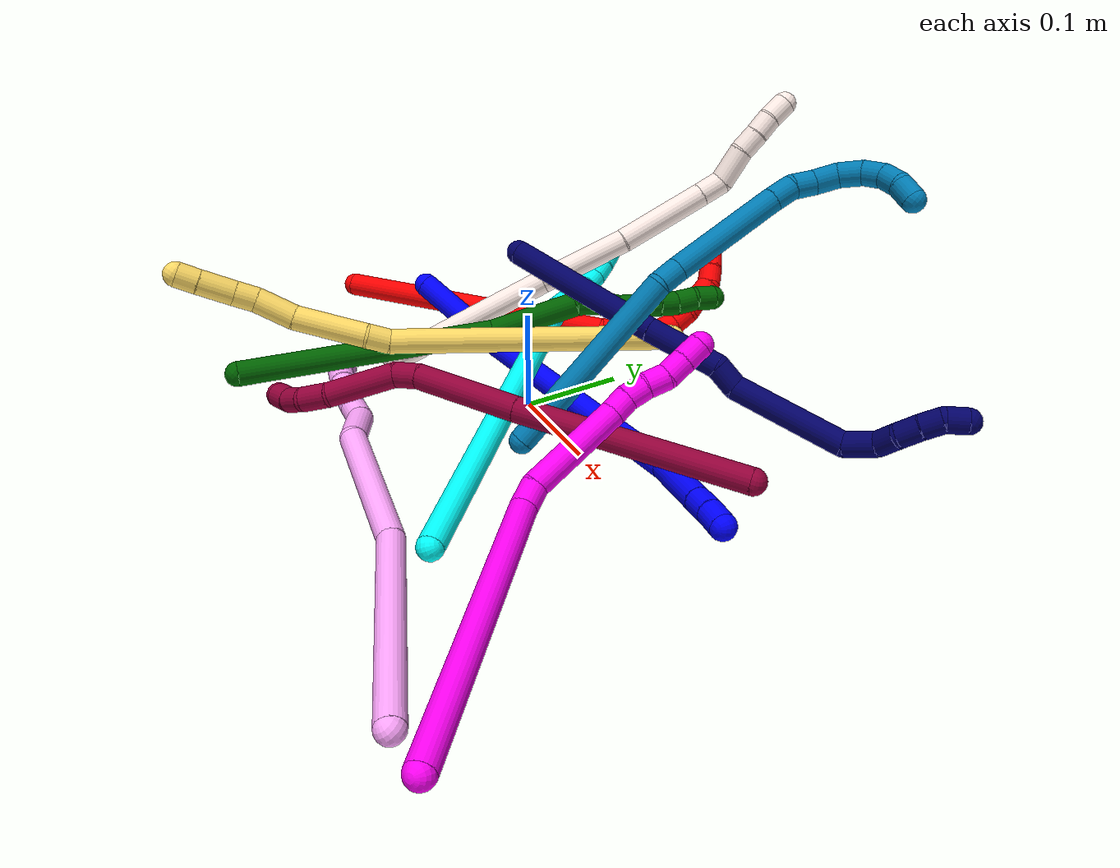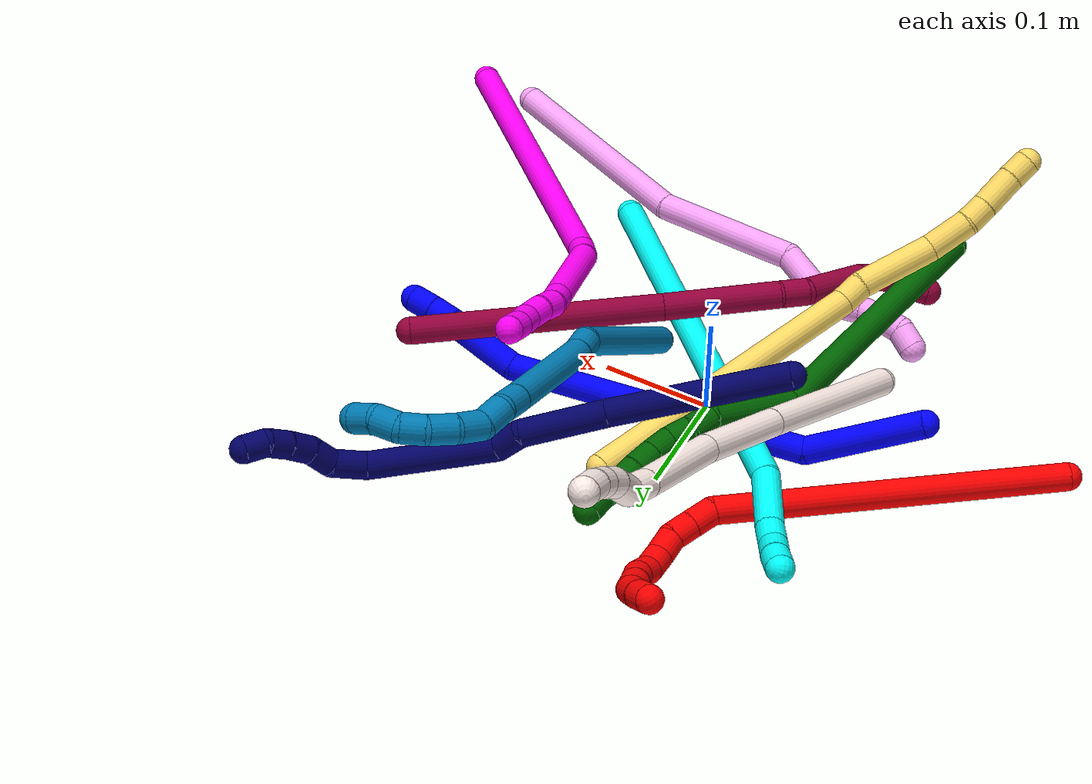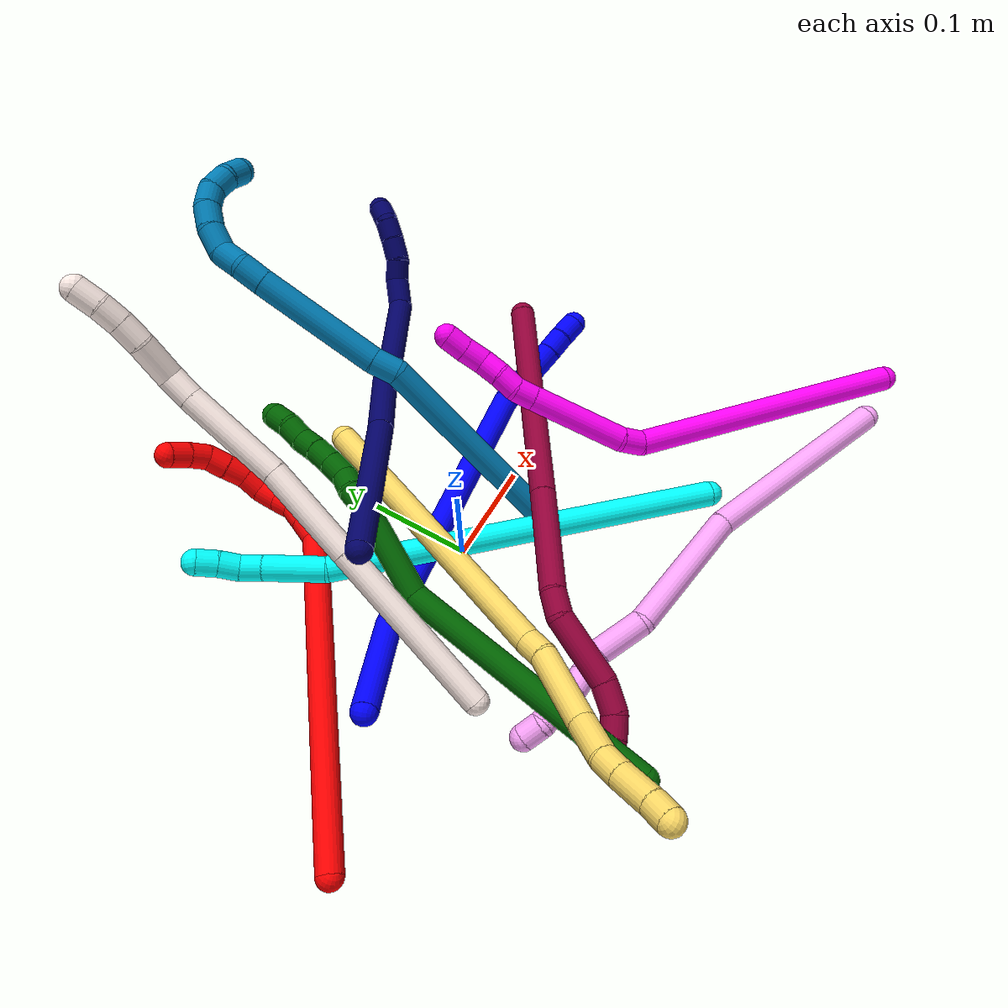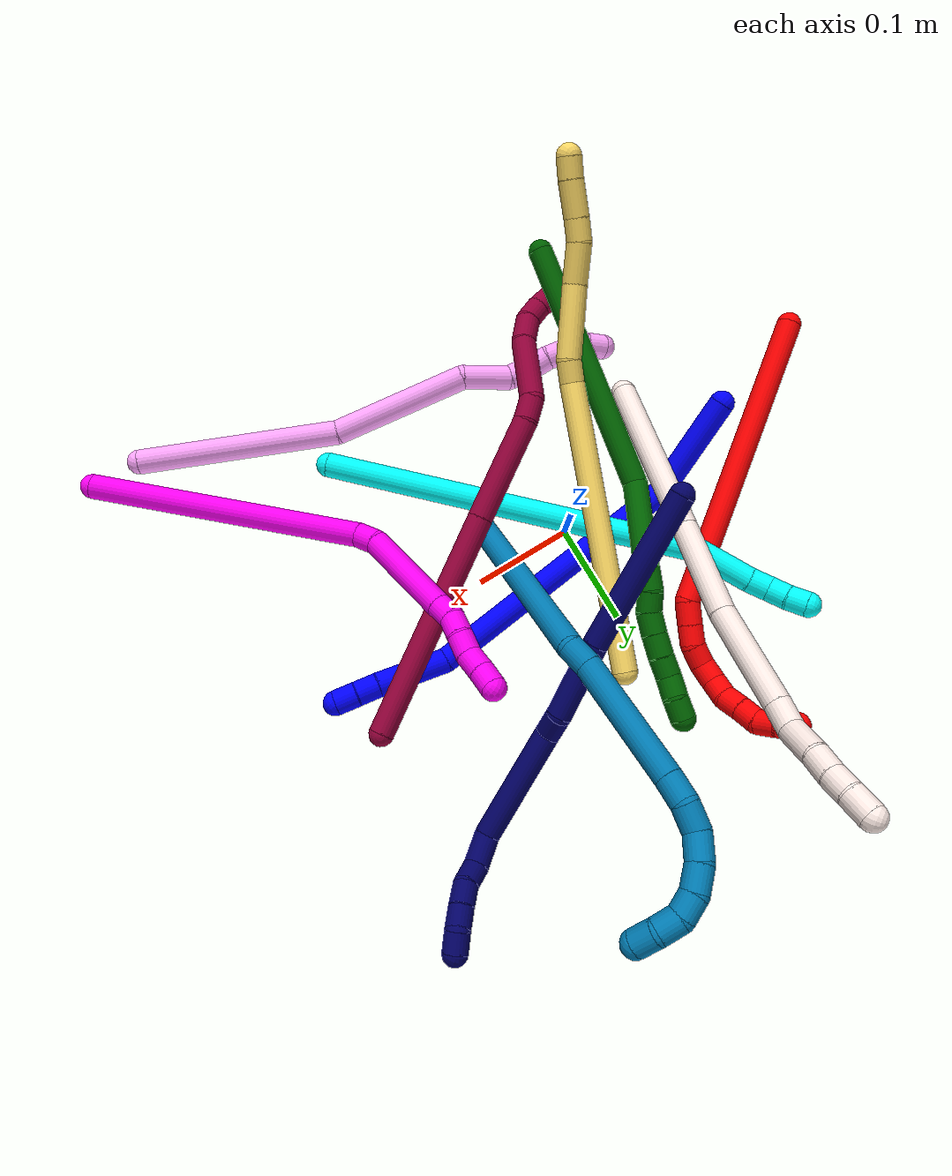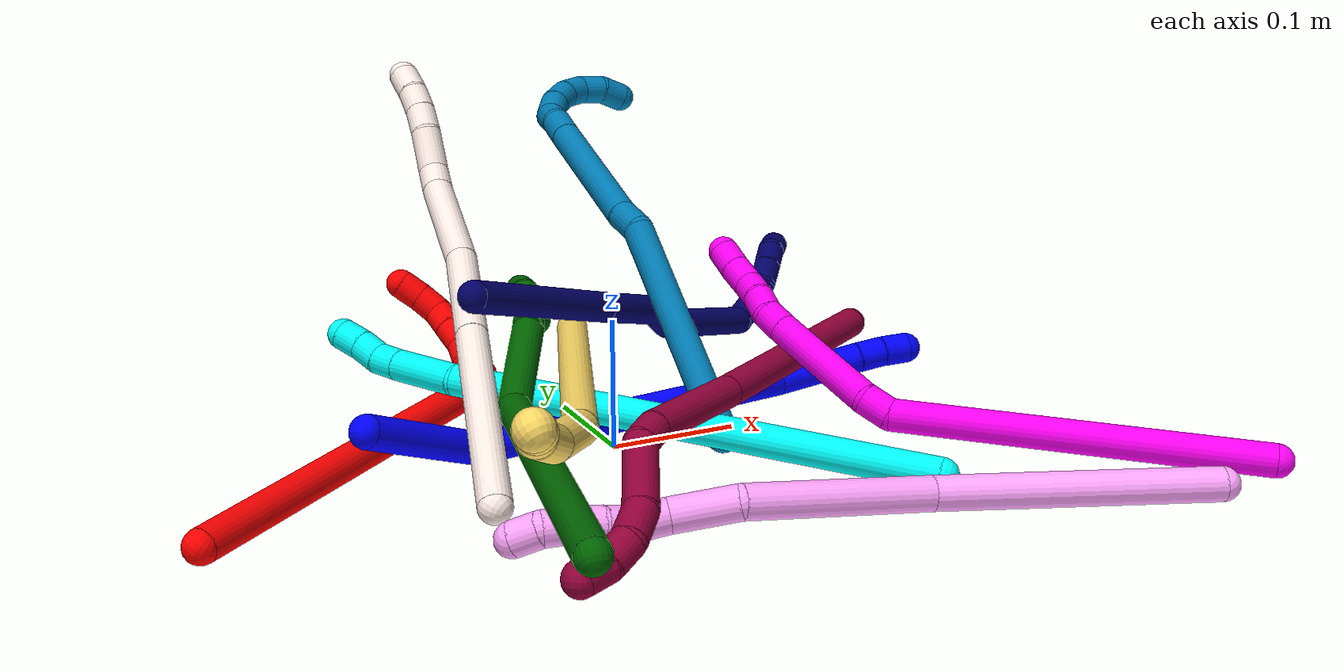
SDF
<sdf version="1.7">
 <world name="default">
  <plugin name="TubeGeneratorPlugin" filename="libtube_generator_plugin.so"/>
  <model name="photoneo_s_sensor">
   <static>1</static>
   <pose>0 0 2 1.57079 1.57079 3.14159</pose>
   <link name="link">
    <inertial><mass>0.1</mass></inertial>
    <sensor name="sensor" type="depth">
     <update_rate>30</update_rate>
     <camera>
      <horizontal_fov>1.22</horizontal_fov>
      <image><width>1920</width><height>1200</height><format>B8G8R8</format></image>
      <clip><near>0.1</near><far>4</far></clip>
      <depth_camera><output>points</output></depth_camera>
     </camera>
     <plugin name="camera_plugin" filename="libgazebo_ros_depth_camera.so">
      <baseline>0.2</baseline>
      <alwaysOn>1</alwaysOn>
      <updateRate>0.0</updateRate>
      <cameraName>camera_ir</cameraName>
      <imageTopicName>/camera/color/image_raw</imageTopicName>
      <cameraInfoTopicName>/camera/color/camera_info</cameraInfoTopicName>
      <depthImageTopicName>/camera/depth/image_raw</depthImageTopicName>
      <depthImageCameraInfoTopicName>/camera/depth/camera_info</depthImageCameraInfoTopicName>
      <pointCloudTopicName>/camera/depth/points</pointCloudTopicName>
      <frameName>fr_optical</frameName>
      <pointCloudCutoff>0.1</pointCloudCutoff>
      <pointCloudCutoffMax>2.0</pointCloudCutoffMax>
      <distortionK1>0</distortionK1>
      <distortionK2>0</distortionK2>
      <distortionK3>0</distortionK3>
      <distortionT1>0</distortionT1>
      <distortionT2>0</distortionT2>
      <CxPrime>0</CxPrime>
      <Cx>0</Cx>
      <Cy>0</Cy>
      <focalLength>0</focalLength>
      <hackBaseline>0</hackBaseline>
     </plugin>
    </sensor>
   </link>
  </model>
  <gravity>0 0 -9.8</gravity>
  <magnetic_field>6e-06 2.3e-05 -4.2e-05</magnetic_field>
  <atmosphere type="adiabatic"/>
  <physics name="default_physics" default="0" type="ode">
   <max_step_size>0.003</max_step_size>
   <real_time_factor>1</real_time_factor>
   <real_time_update_rate>1000</real_time_update_rate>
   <max_contacts>10000</max_contacts>
   <ode>
    <solver>
     <type>quick</type>
     <iters>100</iters>
     <sor>1.3</sor>
     <use_dynamic_moi_rescaling>0</use_dynamic_moi_rescaling>
    </solver>
    <constraints>
     <contact_max_correcting_vel>0</contact_max_correcting_vel>
     <contact_surface_layer>0.001</contact_surface_layer>
     <cfm>0</cfm>
     <erp>0.2</erp>
    </constraints>
   </ode>
  </physics>
  <scene><ambient>0.4 0.4 0.4 1</ambient><background>0.7 0.7 0.7 1</background><shadows>0</shadows></scene>
  <audio><device>default</device></audio>
  <spherical_coordinates>
   <surface_model>EARTH_WGS84</surface_model>
   <latitude_deg>0</latitude_deg>
   <longitude_deg>0</longitude_deg>
   <elevation>0</elevation>
   <heading_deg>0</heading_deg>
  </spherical_coordinates>
  <model name="bin">
   <static>1</static>
   <link name="bottom">
    <collision name="collision-bottom">
     <pose>0 0 -0.01 0 -0 0</pose>
     <geometry><box><size>0.8 0.6 0.02</size></box></geometry>
     <surface>
      <friction><ode><mu>100</mu><mu2>100</mu2></ode></friction>
      <contact><collide_bitmask>65535</collide_bitmask></contact>
     </surface>
    </collision>
   </link>
   <link name="west_wall">
    <collision name="collision-west_wall">
     <pose>-0.41 0 0.1 0 -0 0</pose>
     <geometry><box><size>0.02 0.6 0.2</size></box></geometry>
     <surface>
      <friction><ode><mu>100</mu><mu2>100</mu2></ode></friction>
      <contact><collide_bitmask>65535</collide_bitmask></contact>
     </surface>
    </collision>
   </link>
   <link name="east_wall">
    <collision name="collision-east_wall">
     <pose>0.41 0 0.1 0 -0 0</pose>
     <geometry><box><size>0.02 0.6 0.2</size></box></geometry>
     <surface>
      <friction><ode><mu>100</mu><mu2>100</mu2></ode></friction>
      <contact><collide_bitmask>65535</collide_bitmask></contact>
     </surface>
    </collision>
   </link>
   <link name="south_wall">
    <collision name="collision-south_wall">
     <pose>0 -0.31 0.1 0 -0 0</pose>
     <geometry><box><size>0.8 0.02 0.2</size></box></geometry>
     <surface>
      <friction><ode><mu>100</mu><mu2>100</mu2></ode></friction>
      <contact><collide_bitmask>65535</collide_bitmask></contact>
     </surface>
    </collision>
   </link>
   <link name="north_wall">
    <collision name="collision-north_wall">
     <pose>0 0.31 0.1 0 -0 0</pose>
     <geometry><box><size>0.8 0.02 0.2</size></box></geometry>
     <surface>
      <friction><ode><mu>100</mu><mu2>100</mu2></ode></friction>
      <contact><collide_bitmask>65535</collide_bitmask></contact>
     </surface>
    </collision>
   </link>
  </model>
  <model name="1">
   <static>0</static>
   <link name="1">
    <collision name="collision-cylinder-e_1_1_4">
     <pose>0.047607 0.022094 0.013996 -1.00615 1.06844 -0.629468</pose>
     <geometry><cylinder><radius>0.0125</radius><length>0.108637</length></cylinder></geometry>
     <surface>
      <friction><ode><mu>1.16</mu><mu2>1.16</mu2><slip1>0</slip1><slip2>0</slip2></ode></friction>
      <contact><ode><kp>1e+06</kp><kd>1</kd><max_vel>0</max_vel><min_depth>0.001</min_depth></ode></contact>
     </surface>
    </collision>
    <visual name="visual-cylinder-e_1_1_4">
     <pose>0.047607 0.022094 0.013996 -1.00615 1.06844 -0.629468</pose>
     <geometry><cylinder><radius>0.0125</radius><length>0.108637</length></cylinder></geometry>
     <material><ambient>0 0 1 1</ambient></material>
    </visual>
    <collision name="collision-cylinder-e_2_4_5">
     <pose>0.231479 0.05717 0.013782 -2.40131 1.43048 -2.30141</pose>
     <geometry><cylinder><radius>0.0125</radius><length>0.275234</length></cylinder></geometry>
     <surface>
      <friction><ode><mu>1.16</mu><mu2>1.16</mu2><slip1>0</slip1><slip2>0</slip2></ode></friction>
      <contact><ode><kp>1e+06</kp><kd>1</kd><max_vel>0</max_vel><min_depth>0.001</min_depth></ode></contact>
     </surface>
    </collision>
    <visual name="visual-cylinder-e_2_4_5">
     <pose>0.231479 0.05717 0.013782 -2.40131 1.43048 -2.30141</pose>
     <geometry><cylinder><radius>0.0125</radius><length>0.275234</length></cylinder></geometry>
     <material><ambient>0 0 1 1</ambient></material>
    </visual>
    <collision name="collision-cylinder-e_3_5_6">
     <pose>0.400333 0.069158 -0.015566 3.07604 1.13511 3.03882</pose>
     <geometry><cylinder><radius>0.0125</radius><length>0.071896</length></cylinder></geometry>
     <surface>
      <friction><ode><mu>1.16</mu><mu2>1.16</mu2><slip1>0</slip1><slip2>0</slip2></ode></friction>
      <contact><ode><kp>1e+06</kp><kd>1</kd><max_vel>0</max_vel><min_depth>0.001</min_depth></ode></contact>
     </surface>
    </collision>
    <visual name="visual-cylinder-e_3_5_6">
     <pose>0.400333 0.069158 -0.015566 3.07604 1.13511 3.03882</pose>
     <geometry><cylinder><radius>0.0125</radius><length>0.071896</length></cylinder></geometry>
     <material><ambient>0 0 1 1</ambient></material>
    </visual>
    <collision name="collision-cylinder-e_4_6_7">
     <pose>0.443159 0.068278 -0.03479 -3.11373 1.19096 -3.10046</pose>
     <geometry><cylinder><radius>0.0125</radius><length>0.022044</length></cylinder></geometry>
     <surface>
      <friction><ode><mu>1.16</mu><mu2>1.16</mu2><slip1>0</slip1><slip2>0</slip2></ode></friction>
      <contact><ode><kp>1e+06</kp><kd>1</kd><max_vel>0</max_vel><min_depth>0.001</min_depth></ode></contact>
     </surface>
    </collision>
    <visual name="visual-cylinder-e_4_6_7">
     <pose>0.443159 0.068278 -0.03479 -3.11373 1.19096 -3.10046</pose>
     <geometry><cylinder><radius>0.0125</radius><length>0.022044</length></cylinder></geometry>
     <material><ambient>0 0 1 1</ambient></material>
    </visual>
    <collision name="collision-cylinder-e_5_7_2">
     <pose>0.463685 0.069507 -0.042871 -2.86958 1.18755 -2.74155</pose>
     <geometry><cylinder><radius>0.0125</radius><length>0.02219</length></cylinder></geometry>
     <surface>
      <friction><ode><mu>1.16</mu><mu2>1.16</mu2><slip1>0</slip1><slip2>0</slip2></ode></friction>
      <contact><ode><kp>1e+06</kp><kd>1</kd><max_vel>0</max_vel><min_depth>0.001</min_depth></ode></contact>
     </surface>
    </collision>
    <visual name="visual-cylinder-e_5_7_2">
     <pose>0.463685 0.069507 -0.042871 -2.86958 1.18755 -2.74155</pose>
     <geometry><cylinder><radius>0.0125</radius><length>0.02219</length></cylinder></geometry>
     <material><ambient>0 0 1 1</ambient></material>
    </visual>
    <collision name="collision-sphere-2">
     <pose>0.473975 0.070621 -0.046867 0 -0 0</pose>
     <geometry><sphere><radius>0.0125</radius></sphere></geometry>
     <surface>
      <friction><ode><mu>1.16</mu><mu2>1.16</mu2><slip1>0</slip1><slip2>0</slip2></ode></friction>
      <contact><ode><kp>1e+06</kp><kd>1</kd><max_vel>0</max_vel><min_depth>0.001</min_depth></ode></contact>
     </surface>
    </collision>
    <visual name="visual-sphere-2">
     <pose>0.473975 0.070621 -0.046867 0 -0 0</pose>
     <geometry><sphere><radius>0.0125</radius></sphere></geometry>
     <material><ambient>0 0 1 1</ambient></material>
    </visual>
    <collision name="collision-sphere-7">
     <pose>0.453395 0.068392 -0.038875 0 -0 0</pose>
     <geometry><sphere><radius>0.0125</radius></sphere></geometry>
     <surface>
      <friction><ode><mu>1.16</mu><mu2>1.16</mu2><slip1>0</slip1><slip2>0</slip2></ode></friction>
      <contact><ode><kp>1e+06</kp><kd>1</kd><max_vel>0</max_vel><min_depth>0.001</min_depth></ode></contact>
     </surface>
    </collision>
    <visual name="visual-sphere-7">
     <pose>0.453395 0.068392 -0.038875 0 -0 0</pose>
     <geometry><sphere><radius>0.0125</radius></sphere></geometry>
     <material><ambient>0 0 1 1</ambient></material>
    </visual>
    <collision name="collision-sphere-6">
     <pose>0.432923 0.068164 -0.030705 0 -0 0</pose>
     <geometry><sphere><radius>0.0125</radius></sphere></geometry>
     <surface>
      <friction><ode><mu>1.16</mu><mu2>1.16</mu2><slip1>0</slip1><slip2>0</slip2></ode></friction>
      <contact><ode><kp>1e+06</kp><kd>1</kd><max_vel>0</max_vel><min_depth>0.001</min_depth></ode></contact>
     </surface>
    </collision>
    <visual name="visual-sphere-6">
     <pose>0.432923 0.068164 -0.030705 0 -0 0</pose>
     <geometry><sphere><radius>0.0125</radius></sphere></geometry>
     <material><ambient>0 0 1 1</ambient></material>
    </visual>
    <collision name="collision-sphere-5">
     <pose>0.367744 0.070152 -0.000427 0 -0 0</pose>
     <geometry><sphere><radius>0.0125</radius></sphere></geometry>
     <surface>
      <friction><ode><mu>1.16</mu><mu2>1.16</mu2><slip1>0</slip1><slip2>0</slip2></ode></friction>
      <contact><ode><kp>1e+06</kp><kd>1</kd><max_vel>0</max_vel><min_depth>0.001</min_depth></ode></contact>
     </surface>
    </collision>
    <visual name="visual-sphere-5">
     <pose>0.367744 0.070152 -0.000427 0 -0 0</pose>
     <geometry><sphere><radius>0.0125</radius></sphere></geometry>
     <material><ambient>0 0 1 1</ambient></material>
    </visual>
    <collision name="collision-sphere-1">
     <geometry><sphere><radius>0.0125</radius></sphere></geometry>
     <surface>
      <friction><ode><mu>1.16</mu><mu2>1.16</mu2><slip1>0</slip1><slip2>0</slip2></ode></friction>
      <contact><ode><kp>1e+06</kp><kd>1</kd><max_vel>0</max_vel><min_depth>0.001</min_depth></ode></contact>
     </surface>
    </collision>
    <visual name="visual-sphere-1">
     <geometry><sphere><radius>0.0125</radius></sphere></geometry>
     <material><ambient>0 0 1 1</ambient></material>
    </visual>
    <collision name="collision-sphere-4">
     <pose>0.095215 0.044189 0.027991 0 -0 0</pose>
     <geometry><sphere><radius>0.0125</radius></sphere></geometry>
     <surface>
      <friction><ode><mu>1.16</mu><mu2>1.16</mu2><slip1>0</slip1><slip2>0</slip2></ode></friction>
      <contact><ode><kp>1e+06</kp><kd>1</kd><max_vel>0</max_vel><min_depth>0.001</min_depth></ode></contact>
     </surface>
    </collision>
    <visual name="visual-sphere-4">
     <pose>0.095215 0.044189 0.027991 0 -0 0</pose>
     <geometry><sphere><radius>0.0125</radius></sphere></geometry>
     <material><ambient>0 0 1 1</ambient></material>
    </visual>
    <inertial>
     <pose>0.235446 0.05231 0.004953 0 -0 0</pose>
     <mass>0.5</mass>
     <inertia>
      <ixx>-0.000311</ixx>
      <ixy>0</ixy>
      <ixz>0</ixz>
      <iyy>0.001658</iyy>
      <iyz>0</iyz>
      <izz>-0.002075</izz>
     </inertia>
    </inertial>
   </link>
   <pose>-0.194495 -0.024277 0.05401 -1.79337 -0.069787 0.243586</pose>
  </model>
  <model name="2">
   <static>0</static>
   <link name="2">
    <collision name="collision-cylinder-e_1_1_4">
     <pose>0.089903 0.109008 0.067376 -1.01719 0.611769 -0.348548</pose>
     <geometry><cylinder><radius>0.0125</radius><length>0.31308</length></cylinder></geometry>
     <surface>
      <friction><ode><mu>1.16</mu><mu2>1.16</mu2><slip1>0</slip1><slip2>0</slip2></ode></friction>
      <contact><ode><kp>1e+06</kp><kd>1</kd><max_vel>0</max_vel><min_depth>0.001</min_depth></ode></contact>
     </surface>
    </collision>
    <visual name="visual-cylinder-e_1_1_4">
     <pose>0.089903 0.109008 0.067376 -1.01719 0.611769 -0.348548</pose>
     <geometry><cylinder><radius>0.0125</radius><length>0.31308</length></cylinder></geometry>
     <material><ambient>1 0 0 1</ambient></material>
    </visual>
    <collision name="collision-cylinder-e_2_4_5">
     <pose>0.183748 0.229125 0.135699 -1.48568 0.339775 -0.312487</pose>
     <geometry><cylinder><radius>0.0125</radius><length>0.023652</length></cylinder></geometry>
     <surface>
      <friction><ode><mu>1.16</mu><mu2>1.16</mu2><slip1>0</slip1><slip2>0</slip2></ode></friction>
      <contact><ode><kp>1e+06</kp><kd>1</kd><max_vel>0</max_vel><min_depth>0.001</min_depth></ode></contact>
     </surface>
    </collision>
    <visual name="visual-cylinder-e_2_4_5">
     <pose>0.183748 0.229125 0.135699 -1.48568 0.339775 -0.312487</pose>
     <geometry><cylinder><radius>0.0125</radius><length>0.023652</length></cylinder></geometry>
     <material><ambient>1 0 0 1</ambient></material>
    </visual>
    <collision name="collision-cylinder-e_3_5_6">
     <pose>0.190829 0.249921 0.137514 -1.4816 0.312208 -0.285912</pose>
     <geometry><cylinder><radius>0.0125</radius><length>0.020439</length></cylinder></geometry>
     <surface>
      <friction><ode><mu>1.16</mu><mu2>1.16</mu2><slip1>0</slip1><slip2>0</slip2></ode></friction>
      <contact><ode><kp>1e+06</kp><kd>1</kd><max_vel>0</max_vel><min_depth>0.001</min_depth></ode></contact>
     </surface>
    </collision>
    <visual name="visual-cylinder-e_3_5_6">
     <pose>0.190829 0.249921 0.137514 -1.4816 0.312208 -0.285912</pose>
     <geometry><cylinder><radius>0.0125</radius><length>0.020439</length></cylinder></geometry>
     <material><ambient>1 0 0 1</ambient></material>
    </visual>
    <collision name="collision-cylinder-e_4_6_7">
     <pose>0.195257 0.269668 0.136068 -1.79666 0.124285 -0.155967</pose>
     <geometry><cylinder><radius>0.0125</radius><length>0.020804</length></cylinder></geometry>
     <surface>
      <friction><ode><mu>1.16</mu><mu2>1.16</mu2><slip1>0</slip1><slip2>0</slip2></ode></friction>
      <contact><ode><kp>1e+06</kp><kd>1</kd><max_vel>0</max_vel><min_depth>0.001</min_depth></ode></contact>
     </surface>
    </collision>
    <visual name="visual-cylinder-e_4_6_7">
     <pose>0.195257 0.269668 0.136068 -1.79666 0.124285 -0.155967</pose>
     <geometry><cylinder><radius>0.0125</radius><length>0.020804</length></cylinder></geometry>
     <material><ambient>1 0 0 1</ambient></material>
    </visual>
    <collision name="collision-cylinder-e_5_7_8">
     <pose>0.194726 0.290175 0.133896 -1.55744 -0.172497 0.17022</pose>
     <geometry><cylinder><radius>0.0125</radius><length>0.021211</length></cylinder></geometry>
     <surface>
      <friction><ode><mu>1.16</mu><mu2>1.16</mu2><slip1>0</slip1><slip2>0</slip2></ode></friction>
      <contact><ode><kp>1e+06</kp><kd>1</kd><max_vel>0</max_vel><min_depth>0.001</min_depth></ode></contact>
     </surface>
    </collision>
    <visual name="visual-cylinder-e_5_7_8">
     <pose>0.194726 0.290175 0.133896 -1.55744 -0.172497 0.17022</pose>
     <geometry><cylinder><radius>0.0125</radius><length>0.021211</length></cylinder></geometry>
     <material><ambient>1 0 0 1</ambient></material>
    </visual>
    <collision name="collision-cylinder-e_6_8_9">
     <pose>0.189523 0.309434 0.137608 -1.18575 -0.341835 0.231533</pose>
     <geometry><cylinder><radius>0.0125</radius><length>0.020186</length></cylinder></geometry>
     <surface>
      <friction><ode><mu>1.16</mu><mu2>1.16</mu2><slip1>0</slip1><slip2>0</slip2></ode></friction>
      <contact><ode><kp>1e+06</kp><kd>1</kd><max_vel>0</max_vel><min_depth>0.001</min_depth></ode></contact>
     </surface>
    </collision>
    <visual name="visual-cylinder-e_6_8_9">
     <pose>0.189523 0.309434 0.137608 -1.18575 -0.341835 0.231533</pose>
     <geometry><cylinder><radius>0.0125</radius><length>0.020186</length></cylinder></geometry>
     <material><ambient>1 0 0 1</ambient></material>
    </visual>
    <collision name="collision-cylinder-e_7_9_10">
     <pose>0.180032 0.326305 0.143135 -1.33265 -0.634855 0.505598</pose>
     <geometry><cylinder><radius>0.0125</radius><length>0.020598</length></cylinder></geometry>
     <surface>
      <friction><ode><mu>1.16</mu><mu2>1.16</mu2><slip1>0</slip1><slip2>0</slip2></ode></friction>
      <contact><ode><kp>1e+06</kp><kd>1</kd><max_vel>0</max_vel><min_depth>0.001</min_depth></ode></contact>
     </surface>
    </collision>
    <visual name="visual-cylinder-e_7_9_10">
     <pose>0.180032 0.326305 0.143135 -1.33265 -0.634855 0.505598</pose>
     <geometry><cylinder><radius>0.0125</radius><length>0.020598</length></cylinder></geometry>
     <material><ambient>1 0 0 1</ambient></material>
    </visual>
    <collision name="collision-cylinder-e_8_10_11">
     <pose>0.168572 0.34261 0.146968 -1.34709 -0.564198 0.454595</pose>
     <geometry><cylinder><radius>0.0125</radius><length>0.020018</length></cylinder></geometry>
     <surface>
      <friction><ode><mu>1.16</mu><mu2>1.16</mu2><slip1>0</slip1><slip2>0</slip2></ode></friction>
      <contact><ode><kp>1e+06</kp><kd>1</kd><max_vel>0</max_vel><min_depth>0.001</min_depth></ode></contact>
     </surface>
    </collision>
    <visual name="visual-cylinder-e_8_10_11">
     <pose>0.168572 0.34261 0.146968 -1.34709 -0.564198 0.454595</pose>
     <geometry><cylinder><radius>0.0125</radius><length>0.020018</length></cylinder></geometry>
     <material><ambient>1 0 0 1</ambient></material>
    </visual>
    <collision name="collision-cylinder-e_9_11_12">
     <pose>0.154483 0.355695 0.14942 -1.45219 -1.0621 0.961392</pose>
     <geometry><cylinder><radius>0.0125</radius><length>0.020007</length></cylinder></geometry>
     <surface>
      <friction><ode><mu>1.16</mu><mu2>1.16</mu2><slip1>0</slip1><slip2>0</slip2></ode></friction>
      <contact><ode><kp>1e+06</kp><kd>1</kd><max_vel>0</max_vel><min_depth>0.001</min_depth></ode></contact>
     </surface>
    </collision>
    <visual name="visual-cylinder-e_9_11_12">
     <pose>0.154483 0.355695 0.14942 -1.45219 -1.0621 0.961392</pose>
     <geometry><cylinder><radius>0.0125</radius><length>0.020007</length></cylinder></geometry>
     <material><ambient>1 0 0 1</ambient></material>
    </visual>
    <collision name="collision-cylinder-e_10_12_2">
     <pose>0.136498 0.36434 0.149811 -1.61971 -1.17988 1.22553</pose>
     <geometry><cylinder><radius>0.0125</radius><length>0.020006</length></cylinder></geometry>
     <surface>
      <friction><ode><mu>1.16</mu><mu2>1.16</mu2><slip1>0</slip1><slip2>0</slip2></ode></friction>
      <contact><ode><kp>1e+06</kp><kd>1</kd><max_vel>0</max_vel><min_depth>0.001</min_depth></ode></contact>
     </surface>
    </collision>
    <visual name="visual-cylinder-e_10_12_2">
     <pose>0.136498 0.36434 0.149811 -1.61971 -1.17988 1.22553</pose>
     <geometry><cylinder><radius>0.0125</radius><length>0.020006</length></cylinder></geometry>
     <material><ambient>1 0 0 1</ambient></material>
    </visual>
    <collision name="collision-sphere-2">
     <pose>0.12725 0.368147 0.149624 0 -0 0</pose>
     <geometry><sphere><radius>0.0125</radius></sphere></geometry>
     <surface>
      <friction><ode><mu>1.16</mu><mu2>1.16</mu2><slip1>0</slip1><slip2>0</slip2></ode></friction>
      <contact><ode><kp>1e+06</kp><kd>1</kd><max_vel>0</max_vel><min_depth>0.001</min_depth></ode></contact>
     </surface>
    </collision>
    <visual name="visual-sphere-2">
     <pose>0.12725 0.368147 0.149624 0 -0 0</pose>
     <geometry><sphere><radius>0.0125</radius></sphere></geometry>
     <material><ambient>1 0 0 1</ambient></material>
    </visual>
    <collision name="collision-sphere-12">
     <pose>0.145746 0.360533 0.149997 0 -0 0</pose>
     <geometry><sphere><radius>0.0125</radius></sphere></geometry>
     <surface>
      <friction><ode><mu>1.16</mu><mu2>1.16</mu2><slip1>0</slip1><slip2>0</slip2></ode></friction>
      <contact><ode><kp>1e+06</kp><kd>1</kd><max_vel>0</max_vel><min_depth>0.001</min_depth></ode></contact>
     </surface>
    </collision>
    <visual name="visual-sphere-12">
     <pose>0.145746 0.360533 0.149997 0 -0 0</pose>
     <geometry><sphere><radius>0.0125</radius></sphere></geometry>
     <material><ambient>1 0 0 1</ambient></material>
    </visual>
    <collision name="collision-sphere-11">
     <pose>0.163219 0.350857 0.148844 0 -0 0</pose>
     <geometry><sphere><radius>0.0125</radius></sphere></geometry>
     <surface>
      <friction><ode><mu>1.16</mu><mu2>1.16</mu2><slip1>0</slip1><slip2>0</slip2></ode></friction>
      <contact><ode><kp>1e+06</kp><kd>1</kd><max_vel>0</max_vel><min_depth>0.001</min_depth></ode></contact>
     </surface>
    </collision>
    <visual name="visual-sphere-11">
     <pose>0.163219 0.350857 0.148844 0 -0 0</pose>
     <geometry><sphere><radius>0.0125</radius></sphere></geometry>
     <material><ambient>1 0 0 1</ambient></material>
    </visual>
    <collision name="collision-sphere-10">
     <pose>0.173924 0.334363 0.145091 0 -0 0</pose>
     <geometry><sphere><radius>0.0125</radius></sphere></geometry>
     <surface>
      <friction><ode><mu>1.16</mu><mu2>1.16</mu2><slip1>0</slip1><slip2>0</slip2></ode></friction>
      <contact><ode><kp>1e+06</kp><kd>1</kd><max_vel>0</max_vel><min_depth>0.001</min_depth></ode></contact>
     </surface>
    </collision>
    <visual name="visual-sphere-10">
     <pose>0.173924 0.334363 0.145091 0 -0 0</pose>
     <geometry><sphere><radius>0.0125</radius></sphere></geometry>
     <material><ambient>1 0 0 1</ambient></material>
    </visual>
    <collision name="collision-sphere-9">
     <pose>0.186139 0.318247 0.141179 0 -0 0</pose>
     <geometry><sphere><radius>0.0125</radius></sphere></geometry>
     <surface>
      <friction><ode><mu>1.16</mu><mu2>1.16</mu2><slip1>0</slip1><slip2>0</slip2></ode></friction>
      <contact><ode><kp>1e+06</kp><kd>1</kd><max_vel>0</max_vel><min_depth>0.001</min_depth></ode></contact>
     </surface>
    </collision>
    <visual name="visual-sphere-9">
     <pose>0.186139 0.318247 0.141179 0 -0 0</pose>
     <geometry><sphere><radius>0.0125</radius></sphere></geometry>
     <material><ambient>1 0 0 1</ambient></material>
    </visual>
    <collision name="collision-sphere-4">
     <pose>0.179807 0.218015 0.134752 0 -0 0</pose>
     <geometry><sphere><radius>0.0125</radius></sphere></geometry>
     <surface>
      <friction><ode><mu>1.16</mu><mu2>1.16</mu2><slip1>0</slip1><slip2>0</slip2></ode></friction>
      <contact><ode><kp>1e+06</kp><kd>1</kd><max_vel>0</max_vel><min_depth>0.001</min_depth></ode></contact>
     </surface>
    </collision>
    <visual name="visual-sphere-4">
     <pose>0.179807 0.218015 0.134752 0 -0 0</pose>
     <geometry><sphere><radius>0.0125</radius></sphere></geometry>
     <material><ambient>1 0 0 1</ambient></material>
    </visual>
    <collision name="collision-sphere-1">
     <geometry><sphere><radius>0.0125</radius></sphere></geometry>
     <surface>
      <friction><ode><mu>1.16</mu><mu2>1.16</mu2><slip1>0</slip1><slip2>0</slip2></ode></friction>
      <contact><ode><kp>1e+06</kp><kd>1</kd><max_vel>0</max_vel><min_depth>0.001</min_depth></ode></contact>
     </surface>
    </collision>
    <visual name="visual-sphere-1">
     <geometry><sphere><radius>0.0125</radius></sphere></geometry>
     <material><ambient>1 0 0 1</ambient></material>
    </visual>
    <collision name="collision-sphere-8">
     <pose>0.192906 0.300622 0.134036 0 -0 0</pose>
     <geometry><sphere><radius>0.0125</radius></sphere></geometry>
     <surface>
      <friction><ode><mu>1.16</mu><mu2>1.16</mu2><slip1>0</slip1><slip2>0</slip2></ode></friction>
      <contact><ode><kp>1e+06</kp><kd>1</kd><max_vel>0</max_vel><min_depth>0.001</min_depth></ode></contact>
     </surface>
    </collision>
    <visual name="visual-sphere-8">
     <pose>0.192906 0.300622 0.134036 0 -0 0</pose>
     <geometry><sphere><radius>0.0125</radius></sphere></geometry>
     <material><ambient>1 0 0 1</ambient></material>
    </visual>
    <collision name="collision-sphere-5">
     <pose>0.18769 0.240234 0.136647 0 -0 0</pose>
     <geometry><sphere><radius>0.0125</radius></sphere></geometry>
     <surface>
      <friction><ode><mu>1.16</mu><mu2>1.16</mu2><slip1>0</slip1><slip2>0</slip2></ode></friction>
      <contact><ode><kp>1e+06</kp><kd>1</kd><max_vel>0</max_vel><min_depth>0.001</min_depth></ode></contact>
     </surface>
    </collision>
    <visual name="visual-sphere-5">
     <pose>0.18769 0.240234 0.136647 0 -0 0</pose>
     <geometry><sphere><radius>0.0125</radius></sphere></geometry>
     <material><ambient>1 0 0 1</ambient></material>
    </visual>
    <collision name="collision-sphere-6">
     <pose>0.193968 0.259608 0.13838 0 -0 0</pose>
     <geometry><sphere><radius>0.0125</radius></sphere></geometry>
     <surface>
      <friction><ode><mu>1.16</mu><mu2>1.16</mu2><slip1>0</slip1><slip2>0</slip2></ode></friction>
      <contact><ode><kp>1e+06</kp><kd>1</kd><max_vel>0</max_vel><min_depth>0.001</min_depth></ode></contact>
     </surface>
    </collision>
    <visual name="visual-sphere-6">
     <pose>0.193968 0.259608 0.13838 0 -0 0</pose>
     <geometry><sphere><radius>0.0125</radius></sphere></geometry>
     <material><ambient>1 0 0 1</ambient></material>
    </visual>
    <collision name="collision-sphere-7">
     <pose>0.196547 0.279728 0.133757 0 -0 0</pose>
     <geometry><sphere><radius>0.0125</radius></sphere></geometry>
     <surface>
      <friction><ode><mu>1.16</mu><mu2>1.16</mu2><slip1>0</slip1><slip2>0</slip2></ode></friction>
      <contact><ode><kp>1e+06</kp><kd>1</kd><max_vel>0</max_vel><min_depth>0.001</min_depth></ode></contact>
     </surface>
    </collision>
    <visual name="visual-sphere-7">
     <pose>0.196547 0.279728 0.133757 0 -0 0</pose>
     <geometry><sphere><radius>0.0125</radius></sphere></geometry>
     <material><ambient>1 0 0 1</ambient></material>
    </visual>
    <inertial>
     <pose>0.122631 0.181303 0.094879 0 -0 0</pose>
     <mass>0.5</mass>
     <inertia>
      <ixx>0.001281</ixx>
      <ixy>0</ixy>
      <ixz>0</ixz>
      <iyy>0.001015</iyy>
      <iyz>0</iyz>
      <izz>-0.003261</izz>
     </inertia>
    </inertial>
   </link>
   <pose>-0.314949 -0.065169 0.011498 0.062254 0.654776 -0.081423</pose>
  </model>
  <model name="3">
   <static>0</static>
   <link name="3">
    <collision name="collision-cylinder-e_1_1_4">
     <pose>-0.178518 0.0653 0.00337 -1.51923 -1.21969 1.1717</pose>
     <geometry><cylinder><radius>0.0125</radius><length>0.380232</length></cylinder></geometry>
     <surface>
      <friction><ode><mu>1.16</mu><mu2>1.16</mu2><slip1>0</slip1><slip2>0</slip2></ode></friction>
      <contact><ode><kp>1e+06</kp><kd>1</kd><max_vel>0</max_vel><min_depth>0.001</min_depth></ode></contact>
     </surface>
    </collision>
    <visual name="visual-cylinder-e_1_1_4">
     <pose>-0.178518 0.0653 0.00337 -1.51923 -1.21969 1.1717</pose>
     <geometry><cylinder><radius>0.0125</radius><length>0.380232</length></cylinder></geometry>
     <material><ambient>0.003922 1 0.996078 1</ambient></material>
    </visual>
    <collision name="collision-cylinder-e_2_4_5">
     <pose>-0.385415 0.135057 0.000855 -2.4935 -1.31628 2.3219</pose>
     <geometry><cylinder><radius>0.0125</radius><length>0.058649</length></cylinder></geometry>
     <surface>
      <friction><ode><mu>1.16</mu><mu2>1.16</mu2><slip1>0</slip1><slip2>0</slip2></ode></friction>
      <contact><ode><kp>1e+06</kp><kd>1</kd><max_vel>0</max_vel><min_depth>0.001</min_depth></ode></contact>
     </surface>
    </collision>
    <visual name="visual-cylinder-e_2_4_5">
     <pose>-0.385415 0.135057 0.000855 -2.4935 -1.31628 2.3219</pose>
     <geometry><cylinder><radius>0.0125</radius><length>0.058649</length></cylinder></geometry>
     <material><ambient>0.003922 1 0.996078 1</ambient></material>
    </visual>
    <collision name="collision-cylinder-e_3_5_6">
     <pose>-0.423765 0.142301 -0.006925 -2.16779 -1.24495 1.87042</pose>
     <geometry><cylinder><radius>0.0125</radius><length>0.021048</length></cylinder></geometry>
     <surface>
      <friction><ode><mu>1.16</mu><mu2>1.16</mu2><slip1>0</slip1><slip2>0</slip2></ode></friction>
      <contact><ode><kp>1e+06</kp><kd>1</kd><max_vel>0</max_vel><min_depth>0.001</min_depth></ode></contact>
     </surface>
    </collision>
    <visual name="visual-cylinder-e_3_5_6">
     <pose>-0.423765 0.142301 -0.006925 -2.16779 -1.24495 1.87042</pose>
     <geometry><cylinder><radius>0.0125</radius><length>0.021048</length></cylinder></geometry>
     <material><ambient>0.003922 1 0.996078 1</ambient></material>
    </visual>
    <collision name="collision-cylinder-e_4_6_7">
     <pose>-0.441858 0.149706 -0.012449 -2.23678 -0.944615 1.62064</pose>
     <geometry><cylinder><radius>0.0125</radius><length>0.020049</length></cylinder></geometry>
     <surface>
      <friction><ode><mu>1.16</mu><mu2>1.16</mu2><slip1>0</slip1><slip2>0</slip2></ode></friction>
      <contact><ode><kp>1e+06</kp><kd>1</kd><max_vel>0</max_vel><min_depth>0.001</min_depth></ode></contact>
     </surface>
    </collision>
    <visual name="visual-cylinder-e_4_6_7">
     <pose>-0.441858 0.149706 -0.012449 -2.23678 -0.944615 1.62064</pose>
     <geometry><cylinder><radius>0.0125</radius><length>0.020049</length></cylinder></geometry>
     <material><ambient>0.003922 1 0.996078 1</ambient></material>
    </visual>
    <collision name="collision-cylinder-e_5_7_2">
     <pose>-0.45849 0.159019 -0.018486 -2.04478 -1.01591 1.47796</pose>
     <geometry><cylinder><radius>0.0125</radius><length>0.020022</length></cylinder></geometry>
     <surface>
      <friction><ode><mu>1.16</mu><mu2>1.16</mu2><slip1>0</slip1><slip2>0</slip2></ode></friction>
      <contact><ode><kp>1e+06</kp><kd>1</kd><max_vel>0</max_vel><min_depth>0.001</min_depth></ode></contact>
     </surface>
    </collision>
    <visual name="visual-cylinder-e_5_7_2">
     <pose>-0.45849 0.159019 -0.018486 -2.04478 -1.01591 1.47796</pose>
     <geometry><cylinder><radius>0.0125</radius><length>0.020022</length></cylinder></geometry>
     <material><ambient>0.003922 1 0.996078 1</ambient></material>
    </visual>
    <collision name="collision-sphere-2">
     <pose>-0.466999 0.163711 -0.020893 0 -0 0</pose>
     <geometry><sphere><radius>0.0125</radius></sphere></geometry>
     <surface>
      <friction><ode><mu>1.16</mu><mu2>1.16</mu2><slip1>0</slip1><slip2>0</slip2></ode></friction>
      <contact><ode><kp>1e+06</kp><kd>1</kd><max_vel>0</max_vel><min_depth>0.001</min_depth></ode></contact>
     </surface>
    </collision>
    <visual name="visual-sphere-2">
     <pose>-0.466999 0.163711 -0.020893 0 -0 0</pose>
     <geometry><sphere><radius>0.0125</radius></sphere></geometry>
     <material><ambient>0.003922 1 0.996078 1</ambient></material>
    </visual>
    <collision name="collision-sphere-7">
     <pose>-0.449981 0.154326 -0.016079 0 -0 0</pose>
     <geometry><sphere><radius>0.0125</radius></sphere></geometry>
     <surface>
      <friction><ode><mu>1.16</mu><mu2>1.16</mu2><slip1>0</slip1><slip2>0</slip2></ode></friction>
      <contact><ode><kp>1e+06</kp><kd>1</kd><max_vel>0</max_vel><min_depth>0.001</min_depth></ode></contact>
     </surface>
    </collision>
    <visual name="visual-sphere-7">
     <pose>-0.449981 0.154326 -0.016079 0 -0 0</pose>
     <geometry><sphere><radius>0.0125</radius></sphere></geometry>
     <material><ambient>0.003922 1 0.996078 1</ambient></material>
    </visual>
    <collision name="collision-sphere-6">
     <pose>-0.433736 0.145087 -0.008819 0 -0 0</pose>
     <geometry><sphere><radius>0.0125</radius></sphere></geometry>
     <surface>
      <friction><ode><mu>1.16</mu><mu2>1.16</mu2><slip1>0</slip1><slip2>0</slip2></ode></friction>
      <contact><ode><kp>1e+06</kp><kd>1</kd><max_vel>0</max_vel><min_depth>0.001</min_depth></ode></contact>
     </surface>
    </collision>
    <visual name="visual-sphere-6">
     <pose>-0.433736 0.145087 -0.008819 0 -0 0</pose>
     <geometry><sphere><radius>0.0125</radius></sphere></geometry>
     <material><ambient>0.003922 1 0.996078 1</ambient></material>
    </visual>
    <collision name="collision-sphere-5">
     <pose>-0.413795 0.139514 -0.005031 0 -0 0</pose>
     <geometry><sphere><radius>0.0125</radius></sphere></geometry>
     <surface>
      <friction><ode><mu>1.16</mu><mu2>1.16</mu2><slip1>0</slip1><slip2>0</slip2></ode></friction>
      <contact><ode><kp>1e+06</kp><kd>1</kd><max_vel>0</max_vel><min_depth>0.001</min_depth></ode></contact>
     </surface>
    </collision>
    <visual name="visual-sphere-5">
     <pose>-0.413795 0.139514 -0.005031 0 -0 0</pose>
     <geometry><sphere><radius>0.0125</radius></sphere></geometry>
     <material><ambient>0.003922 1 0.996078 1</ambient></material>
    </visual>
    <collision name="collision-sphere-1">
     <geometry><sphere><radius>0.0125</radius></sphere></geometry>
     <surface>
      <friction><ode><mu>1.16</mu><mu2>1.16</mu2><slip1>0</slip1><slip2>0</slip2></ode></friction>
      <contact><ode><kp>1e+06</kp><kd>1</kd><max_vel>0</max_vel><min_depth>0.001</min_depth></ode></contact>
     </surface>
    </collision>
    <visual name="visual-sphere-1">
     <geometry><sphere><radius>0.0125</radius></sphere></geometry>
     <material><ambient>0.003922 1 0.996078 1</ambient></material>
    </visual>
    <collision name="collision-sphere-4">
     <pose>-0.357035 0.1306 0.006741 0 -0 0</pose>
     <geometry><sphere><radius>0.0125</radius></sphere></geometry>
     <surface>
      <friction><ode><mu>1.16</mu><mu2>1.16</mu2><slip1>0</slip1><slip2>0</slip2></ode></friction>
      <contact><ode><kp>1e+06</kp><kd>1</kd><max_vel>0</max_vel><min_depth>0.001</min_depth></ode></contact>
     </surface>
    </collision>
    <visual name="visual-sphere-4">
     <pose>-0.357035 0.1306 0.006741 0 -0 0</pose>
     <geometry><sphere><radius>0.0125</radius></sphere></geometry>
     <material><ambient>0.003922 1 0.996078 1</ambient></material>
    </visual>
    <inertial>
     <pose>-0.234881 0.083861 0.001132 0 -0 0</pose>
     <mass>0.5</mass>
     <inertia>
      <ixx>0.002036</ixx>
      <ixy>0</ixy>
      <ixz>0</ixz>
      <iyy>0.00556</iyy>
      <iyz>0</iyz>
      <izz>0.002753</izz>
     </inertia>
    </inertial>
   </link>
   <pose>0.170982 -0.183075 0.012463 2.08611 -0.219558 -0.975144</pose>
  </model>
  <model name="4">
   <static>0</static>
   <link name="4">
    <collision name="collision-cylinder-e_1_1_4">
     <pose>-0.074997 -0.068329 0.013271 1.37897 -0.822667 -0.690486</pose>
     <geometry><cylinder><radius>0.0125</radius><length>0.204641</length></cylinder></geometry>
     <surface>
      <friction><ode><mu>1.16</mu><mu2>1.16</mu2><slip1>0</slip1><slip2>0</slip2></ode></friction>
      <contact><ode><kp>1e+06</kp><kd>1</kd><max_vel>0</max_vel><min_depth>0.001</min_depth></ode></contact>
     </surface>
    </collision>
    <visual name="visual-cylinder-e_1_1_4">
     <pose>-0.074997 -0.068329 0.013271 1.37897 -0.822667 -0.690486</pose>
     <geometry><cylinder><radius>0.0125</radius><length>0.204641</length></cylinder></geometry>
     <material><ambient>1 0.65098 0.996078 1</ambient></material>
    </visual>
    <collision name="collision-cylinder-e_2_4_5">
     <pose>-0.190943 -0.188011 0.050245 1.13836 -0.626641 -0.4088</pose>
     <geometry><cylinder><radius>0.0125</radius><length>0.139654</length></cylinder></geometry>
     <surface>
      <friction><ode><mu>1.16</mu><mu2>1.16</mu2><slip1>0</slip1><slip2>0</slip2></ode></friction>
      <contact><ode><kp>1e+06</kp><kd>1</kd><max_vel>0</max_vel><min_depth>0.001</min_depth></ode></contact>
     </surface>
    </collision>
    <visual name="visual-cylinder-e_2_4_5">
     <pose>-0.190943 -0.188011 0.050245 1.13836 -0.626641 -0.4088</pose>
     <geometry><cylinder><radius>0.0125</radius><length>0.139654</length></cylinder></geometry>
     <material><ambient>1 0.65098 0.996078 1</ambient></material>
    </visual>
    <collision name="collision-cylinder-e_3_5_6">
     <pose>-0.249293 -0.256465 0.07175 1.6986 -0.790035 -0.885167</pose>
     <geometry><cylinder><radius>0.0125</radius><length>0.048992</length></cylinder></geometry>
     <surface>
      <friction><ode><mu>1.16</mu><mu2>1.16</mu2><slip1>0</slip1><slip2>0</slip2></ode></friction>
      <contact><ode><kp>1e+06</kp><kd>1</kd><max_vel>0</max_vel><min_depth>0.001</min_depth></ode></contact>
     </surface>
    </collision>
    <visual name="visual-cylinder-e_3_5_6">
     <pose>-0.249293 -0.256465 0.07175 1.6986 -0.790035 -0.885167</pose>
     <geometry><cylinder><radius>0.0125</radius><length>0.048992</length></cylinder></geometry>
     <material><ambient>1 0.65098 0.996078 1</ambient></material>
    </visual>
    <collision name="collision-cylinder-e_4_6_7">
     <pose>-0.272966 -0.284341 0.072357 1.31623 -0.512987 -0.400094</pose>
     <geometry><cylinder><radius>0.0125</radius><length>0.025558</length></cylinder></geometry>
     <surface>
      <friction><ode><mu>1.16</mu><mu2>1.16</mu2><slip1>0</slip1><slip2>0</slip2></ode></friction>
      <contact><ode><kp>1e+06</kp><kd>1</kd><max_vel>0</max_vel><min_depth>0.001</min_depth></ode></contact>
     </surface>
    </collision>
    <visual name="visual-cylinder-e_4_6_7">
     <pose>-0.272966 -0.284341 0.072357 1.31623 -0.512987 -0.400094</pose>
     <geometry><cylinder><radius>0.0125</radius><length>0.025558</length></cylinder></geometry>
     <material><ambient>1 0.65098 0.996078 1</ambient></material>
    </visual>
    <collision name="collision-cylinder-e_5_7_8">
     <pose>-0.28458 -0.302183 0.079988 0.971491 -0.558032 -0.30022</pose>
     <geometry><cylinder><radius>0.0125</radius><length>0.020179</length></cylinder></geometry>
     <surface>
      <friction><ode><mu>1.16</mu><mu2>1.16</mu2><slip1>0</slip1><slip2>0</slip2></ode></friction>
      <contact><ode><kp>1e+06</kp><kd>1</kd><max_vel>0</max_vel><min_depth>0.001</min_depth></ode></contact>
     </surface>
    </collision>
    <visual name="visual-cylinder-e_5_7_8">
     <pose>-0.28458 -0.302183 0.079988 0.971491 -0.558032 -0.30022</pose>
     <geometry><cylinder><radius>0.0125</radius><length>0.020179</length></cylinder></geometry>
     <material><ambient>1 0.65098 0.996078 1</ambient></material>
    </visual>
    <collision name="collision-cylinder-e_6_8_9">
     <pose>-0.296238 -0.316385 0.087994 1.15174 -0.679883 -0.451437</pose>
     <geometry><cylinder><radius>0.0125</radius><length>0.020088</length></cylinder></geometry>
     <surface>
      <friction><ode><mu>1.16</mu><mu2>1.16</mu2><slip1>0</slip1><slip2>0</slip2></ode></friction>
      <contact><ode><kp>1e+06</kp><kd>1</kd><max_vel>0</max_vel><min_depth>0.001</min_depth></ode></contact>
     </surface>
    </collision>
    <visual name="visual-cylinder-e_6_8_9">
     <pose>-0.296238 -0.316385 0.087994 1.15174 -0.679883 -0.451437</pose>
     <geometry><cylinder><radius>0.0125</radius><length>0.020088</length></cylinder></geometry>
     <material><ambient>1 0.65098 0.996078 1</ambient></material>
    </visual>
    <collision name="collision-cylinder-e_7_9_10">
     <pose>-0.308885 -0.331525 0.093213 1.32123 -0.654009 -0.515429</pose>
     <geometry><cylinder><radius>0.0125</radius><length>0.020818</length></cylinder></geometry>
     <surface>
      <friction><ode><mu>1.16</mu><mu2>1.16</mu2><slip1>0</slip1><slip2>0</slip2></ode></friction>
      <contact><ode><kp>1e+06</kp><kd>1</kd><max_vel>0</max_vel><min_depth>0.001</min_depth></ode></contact>
     </surface>
    </collision>
    <visual name="visual-cylinder-e_7_9_10">
     <pose>-0.308885 -0.331525 0.093213 1.32123 -0.654009 -0.515429</pose>
     <geometry><cylinder><radius>0.0125</radius><length>0.020818</length></cylinder></geometry>
     <material><ambient>1 0.65098 0.996078 1</ambient></material>
    </visual>
    <collision name="collision-cylinder-e_8_10_2">
     <pose>-0.321603 -0.346826 0.092665 1.91169 -0.689732 -0.940988</pose>
     <geometry><cylinder><radius>0.0125</radius><length>0.02007</length></cylinder></geometry>
     <surface>
      <friction><ode><mu>1.16</mu><mu2>1.16</mu2><slip1>0</slip1><slip2>0</slip2></ode></friction>
      <contact><ode><kp>1e+06</kp><kd>1</kd><max_vel>0</max_vel><min_depth>0.001</min_depth></ode></contact>
     </surface>
    </collision>
    <visual name="visual-cylinder-e_8_10_2">
     <pose>-0.321603 -0.346826 0.092665 1.91169 -0.689732 -0.940988</pose>
     <geometry><cylinder><radius>0.0125</radius><length>0.02007</length></cylinder></geometry>
     <material><ambient>1 0.65098 0.996078 1</ambient></material>
    </visual>
    <collision name="collision-sphere-2">
     <pose>-0.327988 -0.354122 0.090077 0 -0 0</pose>
     <geometry><sphere><radius>0.0125</radius></sphere></geometry>
     <surface>
      <friction><ode><mu>1.16</mu><mu2>1.16</mu2><slip1>0</slip1><slip2>0</slip2></ode></friction>
      <contact><ode><kp>1e+06</kp><kd>1</kd><max_vel>0</max_vel><min_depth>0.001</min_depth></ode></contact>
     </surface>
    </collision>
    <visual name="visual-sphere-2">
     <pose>-0.327988 -0.354122 0.090077 0 -0 0</pose>
     <geometry><sphere><radius>0.0125</radius></sphere></geometry>
     <material><ambient>1 0.65098 0.996078 1</ambient></material>
    </visual>
    <collision name="collision-sphere-10">
     <pose>-0.315217 -0.33953 0.095253 0 -0 0</pose>
     <geometry><sphere><radius>0.0125</radius></sphere></geometry>
     <surface>
      <friction><ode><mu>1.16</mu><mu2>1.16</mu2><slip1>0</slip1><slip2>0</slip2></ode></friction>
      <contact><ode><kp>1e+06</kp><kd>1</kd><max_vel>0</max_vel><min_depth>0.001</min_depth></ode></contact>
     </surface>
    </collision>
    <visual name="visual-sphere-10">
     <pose>-0.315217 -0.33953 0.095253 0 -0 0</pose>
     <geometry><sphere><radius>0.0125</radius></sphere></geometry>
     <material><ambient>1 0.65098 0.996078 1</ambient></material>
    </visual>
    <collision name="collision-sphere-9">
     <pose>-0.302552 -0.32352 0.091173 0 -0 0</pose>
     <geometry><sphere><radius>0.0125</radius></sphere></geometry>
     <surface>
      <friction><ode><mu>1.16</mu><mu2>1.16</mu2><slip1>0</slip1><slip2>0</slip2></ode></friction>
      <contact><ode><kp>1e+06</kp><kd>1</kd><max_vel>0</max_vel><min_depth>0.001</min_depth></ode></contact>
     </surface>
    </collision>
    <visual name="visual-sphere-9">
     <pose>-0.302552 -0.32352 0.091173 0 -0 0</pose>
     <geometry><sphere><radius>0.0125</radius></sphere></geometry>
     <material><ambient>1 0.65098 0.996078 1</ambient></material>
    </visual>
    <collision name="collision-sphere-4">
     <pose>-0.149994 -0.136657 0.026541 0 -0 0</pose>
     <geometry><sphere><radius>0.0125</radius></sphere></geometry>
     <surface>
      <friction><ode><mu>1.16</mu><mu2>1.16</mu2><slip1>0</slip1><slip2>0</slip2></ode></friction>
      <contact><ode><kp>1e+06</kp><kd>1</kd><max_vel>0</max_vel><min_depth>0.001</min_depth></ode></contact>
     </surface>
    </collision>
    <visual name="visual-sphere-4">
     <pose>-0.149994 -0.136657 0.026541 0 -0 0</pose>
     <geometry><sphere><radius>0.0125</radius></sphere></geometry>
     <material><ambient>1 0.65098 0.996078 1</ambient></material>
    </visual>
    <collision name="collision-sphere-1">
     <geometry><sphere><radius>0.0125</radius></sphere></geometry>
     <surface>
      <friction><ode><mu>1.16</mu><mu2>1.16</mu2><slip1>0</slip1><slip2>0</slip2></ode></friction>
      <contact><ode><kp>1e+06</kp><kd>1</kd><max_vel>0</max_vel><min_depth>0.001</min_depth></ode></contact>
     </surface>
    </collision>
    <visual name="visual-sphere-1">
     <geometry><sphere><radius>0.0125</radius></sphere></geometry>
     <material><ambient>1 0.65098 0.996078 1</ambient></material>
    </visual>
    <collision name="collision-sphere-8">
     <pose>-0.289923 -0.309251 0.084816 0 -0 0</pose>
     <geometry><sphere><radius>0.0125</radius></sphere></geometry>
     <surface>
      <friction><ode><mu>1.16</mu><mu2>1.16</mu2><slip1>0</slip1><slip2>0</slip2></ode></friction>
      <contact><ode><kp>1e+06</kp><kd>1</kd><max_vel>0</max_vel><min_depth>0.001</min_depth></ode></contact>
     </surface>
    </collision>
    <visual name="visual-sphere-8">
     <pose>-0.289923 -0.309251 0.084816 0 -0 0</pose>
     <geometry><sphere><radius>0.0125</radius></sphere></geometry>
     <material><ambient>1 0.65098 0.996078 1</ambient></material>
    </visual>
    <collision name="collision-sphere-5">
     <pose>-0.231891 -0.239365 0.073948 0 -0 0</pose>
     <geometry><sphere><radius>0.0125</radius></sphere></geometry>
     <surface>
      <friction><ode><mu>1.16</mu><mu2>1.16</mu2><slip1>0</slip1><slip2>0</slip2></ode></friction>
      <contact><ode><kp>1e+06</kp><kd>1</kd><max_vel>0</max_vel><min_depth>0.001</min_depth></ode></contact>
     </surface>
    </collision>
    <visual name="visual-sphere-5">
     <pose>-0.231891 -0.239365 0.073948 0 -0 0</pose>
     <geometry><sphere><radius>0.0125</radius></sphere></geometry>
     <material><ambient>1 0.65098 0.996078 1</ambient></material>
    </visual>
    <collision name="collision-sphere-6">
     <pose>-0.266694 -0.273565 0.069553 0 -0 0</pose>
     <geometry><sphere><radius>0.0125</radius></sphere></geometry>
     <surface>
      <friction><ode><mu>1.16</mu><mu2>1.16</mu2><slip1>0</slip1><slip2>0</slip2></ode></friction>
      <contact><ode><kp>1e+06</kp><kd>1</kd><max_vel>0</max_vel><min_depth>0.001</min_depth></ode></contact>
     </surface>
    </collision>
    <visual name="visual-sphere-6">
     <pose>-0.266694 -0.273565 0.069553 0 -0 0</pose>
     <geometry><sphere><radius>0.0125</radius></sphere></geometry>
     <material><ambient>1 0.65098 0.996078 1</ambient></material>
    </visual>
    <collision name="collision-sphere-7">
     <pose>-0.279238 -0.295116 0.075161 0 -0 0</pose>
     <geometry><sphere><radius>0.0125</radius></sphere></geometry>
     <surface>
      <friction><ode><mu>1.16</mu><mu2>1.16</mu2><slip1>0</slip1><slip2>0</slip2></ode></friction>
      <contact><ode><kp>1e+06</kp><kd>1</kd><max_vel>0</max_vel><min_depth>0.001</min_depth></ode></contact>
     </surface>
    </collision>
    <visual name="visual-sphere-7">
     <pose>-0.279238 -0.295116 0.075161 0 -0 0</pose>
     <geometry><sphere><radius>0.0125</radius></sphere></geometry>
     <material><ambient>1 0.65098 0.996078 1</ambient></material>
    </visual>
    <inertial>
     <pose>-0.171563 -0.172774 0.044558 0 -0 0</pose>
     <mass>0.5</mass>
     <inertia><ixx>0.00014</ixx><ixy>0</ixy><ixz>0</ixz><iyy>0.00016</iyy><iyz>0</iyz><izz>0.001353</izz></inertia>
    </inertial>
   </link>
   <pose>0.335013 -0.285508 0.012454 0.542051 0.308435 -1.08296</pose>
  </model>
  <model name="5">
   <static>0</static>
   <link name="5">
    <collision name="collision-cylinder-e_1_1_4">
     <pose>-0.022646 -0.115559 -0.08104 2.18238 -0.159092 -0.304162</pose>
     <geometry><cylinder><radius>0.0125</radius><length>0.285896</length></cylinder></geometry>
     <surface>
      <friction><ode><mu>1.16</mu><mu2>1.16</mu2><slip1>0</slip1><slip2>0</slip2></ode></friction>
      <contact><ode><kp>1e+06</kp><kd>1</kd><max_vel>0</max_vel><min_depth>0.001</min_depth></ode></contact>
     </surface>
    </collision>
    <visual name="visual-cylinder-e_1_1_4">
     <pose>-0.022646 -0.115559 -0.08104 2.18238 -0.159092 -0.304162</pose>
     <geometry><cylinder><radius>0.0125</radius><length>0.285896</length></cylinder></geometry>
     <material><ambient>1 0.858824 0.4 1</ambient></material>
    </visual>
    <collision name="collision-cylinder-e_2_4_5">
     <pose>-0.045787 -0.241941 -0.165988 1.91738 -0.043017 -0.061263</pose>
     <geometry><cylinder><radius>0.0125</radius><length>0.023037</length></cylinder></geometry>
     <surface>
      <friction><ode><mu>1.16</mu><mu2>1.16</mu2><slip1>0</slip1><slip2>0</slip2></ode></friction>
      <contact><ode><kp>1e+06</kp><kd>1</kd><max_vel>0</max_vel><min_depth>0.001</min_depth></ode></contact>
     </surface>
    </collision>
    <visual name="visual-cylinder-e_2_4_5">
     <pose>-0.045787 -0.241941 -0.165988 1.91738 -0.043017 -0.061263</pose>
     <geometry><cylinder><radius>0.0125</radius><length>0.023037</length></cylinder></geometry>
     <material><ambient>1 0.858824 0.4 1</ambient></material>
    </visual>
    <collision name="collision-cylinder-e_3_5_6">
     <pose>-0.057038 -0.285231 -0.18165 1.91811 -0.301956 -0.427121</pose>
     <geometry><cylinder><radius>0.0125</radius><length>0.072329</length></cylinder></geometry>
     <surface>
      <friction><ode><mu>1.16</mu><mu2>1.16</mu2><slip1>0</slip1><slip2>0</slip2></ode></friction>
      <contact><ode><kp>1e+06</kp><kd>1</kd><max_vel>0</max_vel><min_depth>0.001</min_depth></ode></contact>
     </surface>
    </collision>
    <visual name="visual-cylinder-e_3_5_6">
     <pose>-0.057038 -0.285231 -0.18165 1.91811 -0.301956 -0.427121</pose>
     <geometry><cylinder><radius>0.0125</radius><length>0.072329</length></cylinder></geometry>
     <material><ambient>1 0.858824 0.4 1</ambient></material>
    </visual>
    <collision name="collision-cylinder-e_4_6_7">
     <pose>-0.071888 -0.337163 -0.196301 1.71864 -0.205197 -0.237733</pose>
     <geometry><cylinder><radius>0.0125</radius><length>0.040203</length></cylinder></geometry>
     <surface>
      <friction><ode><mu>1.16</mu><mu2>1.16</mu2><slip1>0</slip1><slip2>0</slip2></ode></friction>
      <contact><ode><kp>1e+06</kp><kd>1</kd><max_vel>0</max_vel><min_depth>0.001</min_depth></ode></contact>
     </surface>
    </collision>
    <visual name="visual-cylinder-e_4_6_7">
     <pose>-0.071888 -0.337163 -0.196301 1.71864 -0.205197 -0.237733</pose>
     <geometry><cylinder><radius>0.0125</radius><length>0.040203</length></cylinder></geometry>
     <material><ambient>1 0.858824 0.4 1</ambient></material>
    </visual>
    <collision name="collision-cylinder-e_5_7_8">
     <pose>-0.076328 -0.367247 -0.202467 1.8692 -0.030981 -0.04194</pose>
     <geometry><cylinder><radius>0.0125</radius><length>0.022232</length></cylinder></geometry>
     <surface>
      <friction><ode><mu>1.16</mu><mu2>1.16</mu2><slip1>0</slip1><slip2>0</slip2></ode></friction>
      <contact><ode><kp>1e+06</kp><kd>1</kd><max_vel>0</max_vel><min_depth>0.001</min_depth></ode></contact>
     </surface>
    </collision>
    <visual name="visual-cylinder-e_5_7_8">
     <pose>-0.076328 -0.367247 -0.202467 1.8692 -0.030981 -0.04194</pose>
     <geometry><cylinder><radius>0.0125</radius><length>0.022232</length></cylinder></geometry>
     <material><ambient>1 0.858824 0.4 1</ambient></material>
    </visual>
    <collision name="collision-cylinder-e_6_8_9">
     <pose>-0.076279 -0.394821 -0.210629 1.85193 0.022334 0.029695</pose>
     <geometry><cylinder><radius>0.0125</radius><length>0.035303</length></cylinder></geometry>
     <surface>
      <friction><ode><mu>1.16</mu><mu2>1.16</mu2><slip1>0</slip1><slip2>0</slip2></ode></friction>
      <contact><ode><kp>1e+06</kp><kd>1</kd><max_vel>0</max_vel><min_depth>0.001</min_depth></ode></contact>
     </surface>
    </collision>
    <visual name="visual-cylinder-e_6_8_9">
     <pose>-0.076279 -0.394821 -0.210629 1.85193 0.022334 0.029695</pose>
     <geometry><cylinder><radius>0.0125</radius><length>0.035303</length></cylinder></geometry>
     <material><ambient>1 0.858824 0.4 1</ambient></material>
    </visual>
    <collision name="collision-cylinder-e_7_9_2">
     <pose>-0.076318 -0.421929 -0.218167 1.82526 -0.041314 -0.05343</pose>
     <geometry><cylinder><radius>0.0125</radius><length>0.021001</length></cylinder></geometry>
     <surface>
      <friction><ode><mu>1.16</mu><mu2>1.16</mu2><slip1>0</slip1><slip2>0</slip2></ode></friction>
      <contact><ode><kp>1e+06</kp><kd>1</kd><max_vel>0</max_vel><min_depth>0.001</min_depth></ode></contact>
     </surface>
    </collision>
    <visual name="visual-cylinder-e_7_9_2">
     <pose>-0.076318 -0.421929 -0.218167 1.82526 -0.041314 -0.05343</pose>
     <geometry><cylinder><radius>0.0125</radius><length>0.021001</length></cylinder></geometry>
     <material><ambient>1 0.858824 0.4 1</ambient></material>
    </visual>
    <collision name="collision-sphere-2">
     <pose>-0.076752 -0.432083 -0.220808 0 -0 0</pose>
     <geometry><sphere><radius>0.0125</radius></sphere></geometry>
     <surface>
      <friction><ode><mu>1.16</mu><mu2>1.16</mu2><slip1>0</slip1><slip2>0</slip2></ode></friction>
      <contact><ode><kp>1e+06</kp><kd>1</kd><max_vel>0</max_vel><min_depth>0.001</min_depth></ode></contact>
     </surface>
    </collision>
    <visual name="visual-sphere-2">
     <pose>-0.076752 -0.432083 -0.220808 0 -0 0</pose>
     <geometry><sphere><radius>0.0125</radius></sphere></geometry>
     <material><ambient>1 0.858824 0.4 1</ambient></material>
    </visual>
    <collision name="collision-sphere-9">
     <pose>-0.075884 -0.411776 -0.215526 0 -0 0</pose>
     <geometry><sphere><radius>0.0125</radius></sphere></geometry>
     <surface>
      <friction><ode><mu>1.16</mu><mu2>1.16</mu2><slip1>0</slip1><slip2>0</slip2></ode></friction>
      <contact><ode><kp>1e+06</kp><kd>1</kd><max_vel>0</max_vel><min_depth>0.001</min_depth></ode></contact>
     </surface>
    </collision>
    <visual name="visual-sphere-9">
     <pose>-0.075884 -0.411776 -0.215526 0 -0 0</pose>
     <geometry><sphere><radius>0.0125</radius></sphere></geometry>
     <material><ambient>1 0.858824 0.4 1</ambient></material>
    </visual>
    <collision name="collision-sphere-4">
     <pose>-0.045292 -0.231118 -0.162079 0 -0 0</pose>
     <geometry><sphere><radius>0.0125</radius></sphere></geometry>
     <surface>
      <friction><ode><mu>1.16</mu><mu2>1.16</mu2><slip1>0</slip1><slip2>0</slip2></ode></friction>
      <contact><ode><kp>1e+06</kp><kd>1</kd><max_vel>0</max_vel><min_depth>0.001</min_depth></ode></contact>
     </surface>
    </collision>
    <visual name="visual-sphere-4">
     <pose>-0.045292 -0.231118 -0.162079 0 -0 0</pose>
     <geometry><sphere><radius>0.0125</radius></sphere></geometry>
     <material><ambient>1 0.858824 0.4 1</ambient></material>
    </visual>
    <collision name="collision-sphere-1">
     <geometry><sphere><radius>0.0125</radius></sphere></geometry>
     <surface>
      <friction><ode><mu>1.16</mu><mu2>1.16</mu2><slip1>0</slip1><slip2>0</slip2></ode></friction>
      <contact><ode><kp>1e+06</kp><kd>1</kd><max_vel>0</max_vel><min_depth>0.001</min_depth></ode></contact>
     </surface>
    </collision>
    <visual name="visual-sphere-1">
     <geometry><sphere><radius>0.0125</radius></sphere></geometry>
     <material><ambient>1 0.858824 0.4 1</ambient></material>
    </visual>
    <collision name="collision-sphere-8">
     <pose>-0.076673 -0.377867 -0.205733 0 -0 0</pose>
     <geometry><sphere><radius>0.0125</radius></sphere></geometry>
     <surface>
      <friction><ode><mu>1.16</mu><mu2>1.16</mu2><slip1>0</slip1><slip2>0</slip2></ode></friction>
      <contact><ode><kp>1e+06</kp><kd>1</kd><max_vel>0</max_vel><min_depth>0.001</min_depth></ode></contact>
     </surface>
    </collision>
    <visual name="visual-sphere-8">
     <pose>-0.076673 -0.377867 -0.205733 0 -0 0</pose>
     <geometry><sphere><radius>0.0125</radius></sphere></geometry>
     <material><ambient>1 0.858824 0.4 1</ambient></material>
    </visual>
    <collision name="collision-sphere-5">
     <pose>-0.046283 -0.252765 -0.169897 0 -0 0</pose>
     <geometry><sphere><radius>0.0125</radius></sphere></geometry>
     <surface>
      <friction><ode><mu>1.16</mu><mu2>1.16</mu2><slip1>0</slip1><slip2>0</slip2></ode></friction>
      <contact><ode><kp>1e+06</kp><kd>1</kd><max_vel>0</max_vel><min_depth>0.001</min_depth></ode></contact>
     </surface>
    </collision>
    <visual name="visual-sphere-5">
     <pose>-0.046283 -0.252765 -0.169897 0 -0 0</pose>
     <geometry><sphere><radius>0.0125</radius></sphere></geometry>
     <material><ambient>1 0.858824 0.4 1</ambient></material>
    </visual>
    <collision name="collision-sphere-6">
     <pose>-0.067792 -0.317698 -0.193402 0 -0 0</pose>
     <geometry><sphere><radius>0.0125</radius></sphere></geometry>
     <surface>
      <friction><ode><mu>1.16</mu><mu2>1.16</mu2><slip1>0</slip1><slip2>0</slip2></ode></friction>
      <contact><ode><kp>1e+06</kp><kd>1</kd><max_vel>0</max_vel><min_depth>0.001</min_depth></ode></contact>
     </surface>
    </collision>
    <visual name="visual-sphere-6">
     <pose>-0.067792 -0.317698 -0.193402 0 -0 0</pose>
     <geometry><sphere><radius>0.0125</radius></sphere></geometry>
     <material><ambient>1 0.858824 0.4 1</ambient></material>
    </visual>
    <collision name="collision-sphere-7">
     <pose>-0.075984 -0.356628 -0.1992 0 -0 0</pose>
     <geometry><sphere><radius>0.0125</radius></sphere></geometry>
     <surface>
      <friction><ode><mu>1.16</mu><mu2>1.16</mu2><slip1>0</slip1><slip2>0</slip2></ode></friction>
      <contact><ode><kp>1e+06</kp><kd>1</kd><max_vel>0</max_vel><min_depth>0.001</min_depth></ode></contact>
     </surface>
    </collision>
    <visual name="visual-sphere-7">
     <pose>-0.075984 -0.356628 -0.1992 0 -0 0</pose>
     <geometry><sphere><radius>0.0125</radius></sphere></geometry>
     <material><ambient>1 0.858824 0.4 1</ambient></material>
    </visual>
    <inertial>
     <pose>-0.041075 -0.207521 -0.129084 0 -0 0</pose>
     <mass>0.5</mass>
     <inertia>
      <ixx>0.001291</ixx>
      <ixy>0</ixy>
      <ixz>0</ixz>
      <iyy>-0.001635</iyy>
      <iyz>0</iyz>
      <izz>0.001936</izz>
     </inertia>
    </inertial>
   </link>
   <pose>0.028414 0.150583 0.049533 -0.75033 -0.412836 -0.169391</pose>
  </model>
  <model name="6">
   <static>0</static>
   <link name="6">
    <collision name="collision-cylinder-e_1_1_4">
     <pose>-0.026349 0.086369 0.093247 -0.747125 -0.20441 0.080359</pose>
     <geometry><cylinder><radius>0.0125</radius><length>0.259606</length></cylinder></geometry>
     <surface>
      <friction><ode><mu>1.16</mu><mu2>1.16</mu2><slip1>0</slip1><slip2>0</slip2></ode></friction>
      <contact><ode><kp>1e+06</kp><kd>1</kd><max_vel>0</max_vel><min_depth>0.001</min_depth></ode></contact>
     </surface>
    </collision>
    <visual name="visual-cylinder-e_1_1_4">
     <pose>-0.026349 0.086369 0.093247 -0.747125 -0.20441 0.080359</pose>
     <geometry><cylinder><radius>0.0125</radius><length>0.259606</length></cylinder></geometry>
     <material><ambient>0 0.392157 0.003922 1</ambient></material>
    </visual>
    <collision name="collision-cylinder-e_2_4_5">
     <pose>-0.043454 0.195323 0.226228 -0.516852 0.199555 -0.052913</pose>
     <geometry><cylinder><radius>0.0125</radius><length>0.093258</length></cylinder></geometry>
     <surface>
      <friction><ode><mu>1.16</mu><mu2>1.16</mu2><slip1>0</slip1><slip2>0</slip2></ode></friction>
      <contact><ode><kp>1e+06</kp><kd>1</kd><max_vel>0</max_vel><min_depth>0.001</min_depth></ode></contact>
     </surface>
    </collision>
    <visual name="visual-cylinder-e_2_4_5">
     <pose>-0.043454 0.195323 0.226228 -0.516852 0.199555 -0.052913</pose>
     <geometry><cylinder><radius>0.0125</radius><length>0.093258</length></cylinder></geometry>
     <material><ambient>0 0.392157 0.003922 1</ambient></material>
    </visual>
    <collision name="collision-cylinder-e_3_5_6">
     <pose>-0.034313 0.226451 0.273592 -0.841819 -0.00893 0.003997</pose>
     <geometry><cylinder><radius>0.0125</radius><length>0.02291</length></cylinder></geometry>
     <surface>
      <friction><ode><mu>1.16</mu><mu2>1.16</mu2><slip1>0</slip1><slip2>0</slip2></ode></friction>
      <contact><ode><kp>1e+06</kp><kd>1</kd><max_vel>0</max_vel><min_depth>0.001</min_depth></ode></contact>
     </surface>
    </collision>
    <visual name="visual-cylinder-e_3_5_6">
     <pose>-0.034313 0.226451 0.273592 -0.841819 -0.00893 0.003997</pose>
     <geometry><cylinder><radius>0.0125</radius><length>0.02291</length></cylinder></geometry>
     <material><ambient>0 0.392157 0.003922 1</ambient></material>
    </visual>
    <collision name="collision-cylinder-e_4_6_7">
     <pose>-0.033063 0.243824 0.285778 -1.09446 0.135269 -0.082498</pose>
     <geometry><cylinder><radius>0.0125</radius><length>0.020055</length></cylinder></geometry>
     <surface>
      <friction><ode><mu>1.16</mu><mu2>1.16</mu2><slip1>0</slip1><slip2>0</slip2></ode></friction>
      <contact><ode><kp>1e+06</kp><kd>1</kd><max_vel>0</max_vel><min_depth>0.001</min_depth></ode></contact>
     </surface>
    </collision>
    <visual name="visual-cylinder-e_4_6_7">
     <pose>-0.033063 0.243824 0.285778 -1.09446 0.135269 -0.082498</pose>
     <geometry><cylinder><radius>0.0125</radius><length>0.020055</length></cylinder></geometry>
     <material><ambient>0 0.392157 0.003922 1</ambient></material>
    </visual>
    <collision name="collision-cylinder-e_5_7_8">
     <pose>-0.032753 0.260493 0.297539 -0.827526 -0.097556 0.042865</pose>
     <geometry><cylinder><radius>0.0125</radius><length>0.021398</length></cylinder></geometry>
     <surface>
      <friction><ode><mu>1.16</mu><mu2>1.16</mu2><slip1>0</slip1><slip2>0</slip2></ode></friction>
      <contact><ode><kp>1e+06</kp><kd>1</kd><max_vel>0</max_vel><min_depth>0.001</min_depth></ode></contact>
     </surface>
    </collision>
    <visual name="visual-cylinder-e_5_7_8">
     <pose>-0.032753 0.260493 0.297539 -0.827526 -0.097556 0.042865</pose>
     <geometry><cylinder><radius>0.0125</radius><length>0.021398</length></cylinder></geometry>
     <material><ambient>0 0.392157 0.003922 1</ambient></material>
    </visual>
    <collision name="collision-cylinder-e_6_8_9">
     <pose>-0.035353 0.27622 0.312044 -0.824024 -0.14402 0.063028</pose>
     <geometry><cylinder><radius>0.0125</radius><length>0.021717</length></cylinder></geometry>
     <surface>
      <friction><ode><mu>1.16</mu><mu2>1.16</mu2><slip1>0</slip1><slip2>0</slip2></ode></friction>
      <contact><ode><kp>1e+06</kp><kd>1</kd><max_vel>0</max_vel><min_depth>0.001</min_depth></ode></contact>
     </surface>
    </collision>
    <visual name="visual-cylinder-e_6_8_9">
     <pose>-0.035353 0.27622 0.312044 -0.824024 -0.14402 0.063028</pose>
     <geometry><cylinder><radius>0.0125</radius><length>0.021717</length></cylinder></geometry>
     <material><ambient>0 0.392157 0.003922 1</ambient></material>
    </visual>
    <collision name="collision-cylinder-e_7_9_10">
     <pose>-0.039224 0.291398 0.325825 -0.844186 -0.232675 0.104869</pose>
     <geometry><cylinder><radius>0.0125</radius><length>0.020053</length></cylinder></geometry>
     <surface>
      <friction><ode><mu>1.16</mu><mu2>1.16</mu2><slip1>0</slip1><slip2>0</slip2></ode></friction>
      <contact><ode><kp>1e+06</kp><kd>1</kd><max_vel>0</max_vel><min_depth>0.001</min_depth></ode></contact>
     </surface>
    </collision>
    <visual name="visual-cylinder-e_7_9_10">
     <pose>-0.039224 0.291398 0.325825 -0.844186 -0.232675 0.104869</pose>
     <geometry><cylinder><radius>0.0125</radius><length>0.020053</length></cylinder></geometry>
     <material><ambient>0 0.392157 0.003922 1</ambient></material>
    </visual>
    <collision name="collision-cylinder-e_8_10_11">
     <pose>-0.042115 0.30487 0.340555 -0.643001 -0.05614 0.018702</pose>
     <geometry><cylinder><radius>0.0125</radius><length>0.020646</length></cylinder></geometry>
     <surface>
      <friction><ode><mu>1.16</mu><mu2>1.16</mu2><slip1>0</slip1><slip2>0</slip2></ode></friction>
      <contact><ode><kp>1e+06</kp><kd>1</kd><max_vel>0</max_vel><min_depth>0.001</min_depth></ode></contact>
     </surface>
    </collision>
    <visual name="visual-cylinder-e_8_10_11">
     <pose>-0.042115 0.30487 0.340555 -0.643001 -0.05614 0.018702</pose>
     <geometry><cylinder><radius>0.0125</radius><length>0.020646</length></cylinder></geometry>
     <material><ambient>0 0.392157 0.003922 1</ambient></material>
    </visual>
    <collision name="collision-cylinder-e_9_11_2">
     <pose>-0.045125 0.318523 0.355272 -0.857368 -0.2412 0.11066</pose>
     <geometry><cylinder><radius>0.0125</radius><length>0.020357</length></cylinder></geometry>
     <surface>
      <friction><ode><mu>1.16</mu><mu2>1.16</mu2><slip1>0</slip1><slip2>0</slip2></ode></friction>
      <contact><ode><kp>1e+06</kp><kd>1</kd><max_vel>0</max_vel><min_depth>0.001</min_depth></ode></contact>
     </surface>
    </collision>
    <visual name="visual-cylinder-e_9_11_2">
     <pose>-0.045125 0.318523 0.355272 -0.857368 -0.2412 0.11066</pose>
     <geometry><cylinder><radius>0.0125</radius><length>0.020357</length></cylinder></geometry>
     <material><ambient>0 0.392157 0.003922 1</ambient></material>
    </visual>
    <collision name="collision-sphere-2">
     <pose>-0.047556 0.325996 0.36174 0 -0 0</pose>
     <geometry><sphere><radius>0.0125</radius></sphere></geometry>
     <surface>
      <friction><ode><mu>1.16</mu><mu2>1.16</mu2><slip1>0</slip1><slip2>0</slip2></ode></friction>
      <contact><ode><kp>1e+06</kp><kd>1</kd><max_vel>0</max_vel><min_depth>0.001</min_depth></ode></contact>
     </surface>
    </collision>
    <visual name="visual-sphere-2">
     <pose>-0.047556 0.325996 0.36174 0 -0 0</pose>
     <geometry><sphere><radius>0.0125</radius></sphere></geometry>
     <material><ambient>0 0.392157 0.003922 1</ambient></material>
    </visual>
    <collision name="collision-sphere-11">
     <pose>-0.042694 0.31105 0.348803 0 -0 0</pose>
     <geometry><sphere><radius>0.0125</radius></sphere></geometry>
     <surface>
      <friction><ode><mu>1.16</mu><mu2>1.16</mu2><slip1>0</slip1><slip2>0</slip2></ode></friction>
      <contact><ode><kp>1e+06</kp><kd>1</kd><max_vel>0</max_vel><min_depth>0.001</min_depth></ode></contact>
     </surface>
    </collision>
    <visual name="visual-sphere-11">
     <pose>-0.042694 0.31105 0.348803 0 -0 0</pose>
     <geometry><sphere><radius>0.0125</radius></sphere></geometry>
     <material><ambient>0 0.392157 0.003922 1</ambient></material>
    </visual>
    <collision name="collision-sphere-10">
     <pose>-0.041535 0.29869 0.332307 0 -0 0</pose>
     <geometry><sphere><radius>0.0125</radius></sphere></geometry>
     <surface>
      <friction><ode><mu>1.16</mu><mu2>1.16</mu2><slip1>0</slip1><slip2>0</slip2></ode></friction>
      <contact><ode><kp>1e+06</kp><kd>1</kd><max_vel>0</max_vel><min_depth>0.001</min_depth></ode></contact>
     </surface>
    </collision>
    <visual name="visual-sphere-10">
     <pose>-0.041535 0.29869 0.332307 0 -0 0</pose>
     <geometry><sphere><radius>0.0125</radius></sphere></geometry>
     <material><ambient>0 0.392157 0.003922 1</ambient></material>
    </visual>
    <collision name="collision-sphere-9">
     <pose>-0.036912 0.284106 0.319344 0 -0 0</pose>
     <geometry><sphere><radius>0.0125</radius></sphere></geometry>
     <surface>
      <friction><ode><mu>1.16</mu><mu2>1.16</mu2><slip1>0</slip1><slip2>0</slip2></ode></friction>
      <contact><ode><kp>1e+06</kp><kd>1</kd><max_vel>0</max_vel><min_depth>0.001</min_depth></ode></contact>
     </surface>
    </collision>
    <visual name="visual-sphere-9">
     <pose>-0.036912 0.284106 0.319344 0 -0 0</pose>
     <geometry><sphere><radius>0.0125</radius></sphere></geometry>
     <material><ambient>0 0.392157 0.003922 1</ambient></material>
    </visual>
    <collision name="collision-sphere-4">
     <pose>-0.052697 0.172738 0.186494 0 -0 0</pose>
     <geometry><sphere><radius>0.0125</radius></sphere></geometry>
     <surface>
      <friction><ode><mu>1.16</mu><mu2>1.16</mu2><slip1>0</slip1><slip2>0</slip2></ode></friction>
      <contact><ode><kp>1e+06</kp><kd>1</kd><max_vel>0</max_vel><min_depth>0.001</min_depth></ode></contact>
     </surface>
    </collision>
    <visual name="visual-sphere-4">
     <pose>-0.052697 0.172738 0.186494 0 -0 0</pose>
     <geometry><sphere><radius>0.0125</radius></sphere></geometry>
     <material><ambient>0 0.392157 0.003922 1</ambient></material>
    </visual>
    <collision name="collision-sphere-1">
     <geometry><sphere><radius>0.0125</radius></sphere></geometry>
     <surface>
      <friction><ode><mu>1.16</mu><mu2>1.16</mu2><slip1>0</slip1><slip2>0</slip2></ode></friction>
      <contact><ode><kp>1e+06</kp><kd>1</kd><max_vel>0</max_vel><min_depth>0.001</min_depth></ode></contact>
     </surface>
    </collision>
    <visual name="visual-sphere-1">
     <geometry><sphere><radius>0.0125</radius></sphere></geometry>
     <material><ambient>0 0.392157 0.003922 1</ambient></material>
    </visual>
    <collision name="collision-sphere-8">
     <pose>-0.033795 0.268333 0.304745 0 -0 0</pose>
     <geometry><sphere><radius>0.0125</radius></sphere></geometry>
     <surface>
      <friction><ode><mu>1.16</mu><mu2>1.16</mu2><slip1>0</slip1><slip2>0</slip2></ode></friction>
      <contact><ode><kp>1e+06</kp><kd>1</kd><max_vel>0</max_vel><min_depth>0.001</min_depth></ode></contact>
     </surface>
    </collision>
    <visual name="visual-sphere-8">
     <pose>-0.033795 0.268333 0.304745 0 -0 0</pose>
     <geometry><sphere><radius>0.0125</radius></sphere></geometry>
     <material><ambient>0 0.392157 0.003922 1</ambient></material>
    </visual>
    <collision name="collision-sphere-5">
     <pose>-0.03421 0.217907 0.265962 0 -0 0</pose>
     <geometry><sphere><radius>0.0125</radius></sphere></geometry>
     <surface>
      <friction><ode><mu>1.16</mu><mu2>1.16</mu2><slip1>0</slip1><slip2>0</slip2></ode></friction>
      <contact><ode><kp>1e+06</kp><kd>1</kd><max_vel>0</max_vel><min_depth>0.001</min_depth></ode></contact>
     </surface>
    </collision>
    <visual name="visual-sphere-5">
     <pose>-0.03421 0.217907 0.265962 0 -0 0</pose>
     <geometry><sphere><radius>0.0125</radius></sphere></geometry>
     <material><ambient>0 0.392157 0.003922 1</ambient></material>
    </visual>
    <collision name="collision-sphere-6">
     <pose>-0.034415 0.234994 0.281222 0 -0 0</pose>
     <geometry><sphere><radius>0.0125</radius></sphere></geometry>
     <surface>
      <friction><ode><mu>1.16</mu><mu2>1.16</mu2><slip1>0</slip1><slip2>0</slip2></ode></friction>
      <contact><ode><kp>1e+06</kp><kd>1</kd><max_vel>0</max_vel><min_depth>0.001</min_depth></ode></contact>
     </surface>
    </collision>
    <visual name="visual-sphere-6">
     <pose>-0.034415 0.234994 0.281222 0 -0 0</pose>
     <geometry><sphere><radius>0.0125</radius></sphere></geometry>
     <material><ambient>0 0.392157 0.003922 1</ambient></material>
    </visual>
    <collision name="collision-sphere-7">
     <pose>-0.031711 0.252653 0.290333 0 -0 0</pose>
     <geometry><sphere><radius>0.0125</radius></sphere></geometry>
     <surface>
      <friction><ode><mu>1.16</mu><mu2>1.16</mu2><slip1>0</slip1><slip2>0</slip2></ode></friction>
      <contact><ode><kp>1e+06</kp><kd>1</kd><max_vel>0</max_vel><min_depth>0.001</min_depth></ode></contact>
     </surface>
    </collision>
    <visual name="visual-sphere-7">
     <pose>-0.031711 0.252653 0.290333 0 -0 0</pose>
     <geometry><sphere><radius>0.0125</radius></sphere></geometry>
     <material><ambient>0 0.392157 0.003922 1</ambient></material>
    </visual>
    <inertial>
     <pose>-0.03277 0.161819 0.182489 0 -0 0</pose>
     <mass>0.5</mass>
     <inertia>
      <ixx>0.001622</ixx>
      <ixy>0</ixy>
      <ixz>0</ixz>
      <iyy>0.001297</iyy>
      <iyz>0</iyz>
      <izz>-0.000706</izz>
     </inertia>
    </inertial>
   </link>
   <pose>-0.12602 -0.255526 0.04406 -0.746348 -0.347705 -0.399094</pose>
  </model>
  <model name="7">
   <static>0</static>
   <link name="7">
    <collision name="collision-cylinder-e_1_1_4">
     <pose>0.013231 0.010385 0.078708 -0.131191 0.165136 -0.010872</pose>
     <geometry><cylinder><radius>0.0125</radius><length>0.16097</length></cylinder></geometry>
     <surface>
      <friction><ode><mu>1.16</mu><mu2>1.16</mu2><slip1>0</slip1><slip2>0</slip2></ode></friction>
      <contact><ode><kp>1e+06</kp><kd>1</kd><max_vel>0</max_vel><min_depth>0.001</min_depth></ode></contact>
     </surface>
    </collision>
    <visual name="visual-cylinder-e_1_1_4">
     <pose>0.013231 0.010385 0.078708 -0.131191 0.165136 -0.010872</pose>
     <geometry><cylinder><radius>0.0125</radius><length>0.16097</length></cylinder></geometry>
     <material><ambient>0.003922 0 0.403922 1</ambient></material>
    </visual>
    <collision name="collision-cylinder-e_2_4_5">
     <pose>0.032861 0.02379 0.195093 -0.079954 0.167733 -0.006725</pose>
     <geometry><cylinder><radius>0.0125</radius><length>0.076673</length></cylinder></geometry>
     <surface>
      <friction><ode><mu>1.16</mu><mu2>1.16</mu2><slip1>0</slip1><slip2>0</slip2></ode></friction>
      <contact><ode><kp>1e+06</kp><kd>1</kd><max_vel>0</max_vel><min_depth>0.001</min_depth></ode></contact>
     </surface>
    </collision>
    <visual name="visual-cylinder-e_2_4_5">
     <pose>0.032861 0.02379 0.195093 -0.079954 0.167733 -0.006725</pose>
     <geometry><cylinder><radius>0.0125</radius><length>0.076673</length></cylinder></geometry>
     <material><ambient>0.003922 0 0.403922 1</ambient></material>
    </visual>
    <collision name="collision-cylinder-e_3_5_6">
     <pose>0.035821 0.029024 0.245213 -0.176216 -0.26582 0.02362</pose>
     <geometry><cylinder><radius>0.0125</radius><length>0.026197</length></cylinder></geometry>
     <surface>
      <friction><ode><mu>1.16</mu><mu2>1.16</mu2><slip1>0</slip1><slip2>0</slip2></ode></friction>
      <contact><ode><kp>1e+06</kp><kd>1</kd><max_vel>0</max_vel><min_depth>0.001</min_depth></ode></contact>
     </surface>
    </collision>
    <visual name="visual-cylinder-e_3_5_6">
     <pose>0.035821 0.029024 0.245213 -0.176216 -0.26582 0.02362</pose>
     <geometry><cylinder><radius>0.0125</radius><length>0.026197</length></cylinder></geometry>
     <material><ambient>0.003922 0 0.403922 1</ambient></material>
    </visual>
    <collision name="collision-cylinder-e_4_6_7">
     <pose>0.045964 0.03896 0.313734 -0.136809 0.235518 -0.01621</pose>
     <geometry><cylinder><radius>0.0125</radius><length>0.116429</length></cylinder></geometry>
     <surface>
      <friction><ode><mu>1.16</mu><mu2>1.16</mu2><slip1>0</slip1><slip2>0</slip2></ode></friction>
      <contact><ode><kp>1e+06</kp><kd>1</kd><max_vel>0</max_vel><min_depth>0.001</min_depth></ode></contact>
     </surface>
    </collision>
    <visual name="visual-cylinder-e_4_6_7">
     <pose>0.045964 0.03896 0.313734 -0.136809 0.235518 -0.01621</pose>
     <geometry><cylinder><radius>0.0125</radius><length>0.116429</length></cylinder></geometry>
     <material><ambient>0.003922 0 0.403922 1</ambient></material>
    </visual>
    <collision name="collision-cylinder-e_5_7_8">
     <pose>0.069796 0.044815 0.382026 0.151536 0.692433 0.054757</pose>
     <geometry><cylinder><radius>0.0125</radius><length>0.032104</length></cylinder></geometry>
     <surface>
      <friction><ode><mu>1.16</mu><mu2>1.16</mu2><slip1>0</slip1><slip2>0</slip2></ode></friction>
      <contact><ode><kp>1e+06</kp><kd>1</kd><max_vel>0</max_vel><min_depth>0.001</min_depth></ode></contact>
     </surface>
    </collision>
    <visual name="visual-cylinder-e_5_7_8">
     <pose>0.069796 0.044815 0.382026 0.151536 0.692433 0.054757</pose>
     <geometry><cylinder><radius>0.0125</radius><length>0.032104</length></cylinder></geometry>
     <material><ambient>0.003922 0 0.403922 1</ambient></material>
    </visual>
    <collision name="collision-cylinder-e_6_8_9">
     <pose>0.090788 0.042874 0.398486 0.017842 1.19432 0.012132</pose>
     <geometry><cylinder><radius>0.0125</radius><length>0.023107</length></cylinder></geometry>
     <surface>
      <friction><ode><mu>1.16</mu><mu2>1.16</mu2><slip1>0</slip1><slip2>0</slip2></ode></friction>
      <contact><ode><kp>1e+06</kp><kd>1</kd><max_vel>0</max_vel><min_depth>0.001</min_depth></ode></contact>
     </surface>
    </collision>
    <visual name="visual-cylinder-e_6_8_9">
     <pose>0.090788 0.042874 0.398486 0.017842 1.19432 0.012132</pose>
     <geometry><cylinder><radius>0.0125</radius><length>0.023107</length></cylinder></geometry>
     <material><ambient>0.003922 0 0.403922 1</ambient></material>
    </visual>
    <collision name="collision-cylinder-e_7_9_10">
     <pose>0.11078 0.039648 0.408577 0.494497 0.94818 0.257603</pose>
     <geometry><cylinder><radius>0.0125</radius><length>0.022768</length></cylinder></geometry>
     <surface>
      <friction><ode><mu>1.16</mu><mu2>1.16</mu2><slip1>0</slip1><slip2>0</slip2></ode></friction>
      <contact><ode><kp>1e+06</kp><kd>1</kd><max_vel>0</max_vel><min_depth>0.001</min_depth></ode></contact>
     </surface>
    </collision>
    <visual name="visual-cylinder-e_7_9_10">
     <pose>0.11078 0.039648 0.408577 0.494497 0.94818 0.257603</pose>
     <geometry><cylinder><radius>0.0125</radius><length>0.022768</length></cylinder></geometry>
     <material><ambient>0.003922 0 0.403922 1</ambient></material>
    </visual>
    <collision name="collision-cylinder-e_8_10_11">
     <pose>0.127995 0.033177 0.42058 0.494412 0.850063 0.227468</pose>
     <geometry><cylinder><radius>0.0125</radius><length>0.021207</length></cylinder></geometry>
     <surface>
      <friction><ode><mu>1.16</mu><mu2>1.16</mu2><slip1>0</slip1><slip2>0</slip2></ode></friction>
      <contact><ode><kp>1e+06</kp><kd>1</kd><max_vel>0</max_vel><min_depth>0.001</min_depth></ode></contact>
     </surface>
    </collision>
    <visual name="visual-cylinder-e_8_10_11">
     <pose>0.127995 0.033177 0.42058 0.494412 0.850063 0.227468</pose>
     <geometry><cylinder><radius>0.0125</radius><length>0.021207</length></cylinder></geometry>
     <material><ambient>0.003922 0 0.403922 1</ambient></material>
    </visual>
    <collision name="collision-cylinder-e_9_11_2">
     <pose>0.139809 0.026606 0.435693 0.348187 0.383857 0.068325</pose>
     <geometry><cylinder><radius>0.0125</radius><length>0.020546</length></cylinder></geometry>
     <surface>
      <friction><ode><mu>1.16</mu><mu2>1.16</mu2><slip1>0</slip1><slip2>0</slip2></ode></friction>
      <contact><ode><kp>1e+06</kp><kd>1</kd><max_vel>0</max_vel><min_depth>0.001</min_depth></ode></contact>
     </surface>
    </collision>
    <visual name="visual-cylinder-e_9_11_2">
     <pose>0.139809 0.026606 0.435693 0.348187 0.383857 0.068325</pose>
     <geometry><cylinder><radius>0.0125</radius><length>0.020546</length></cylinder></geometry>
     <material><ambient>0.003922 0 0.403922 1</ambient></material>
    </visual>
    <collision name="collision-sphere-2">
     <pose>0.143656 0.023356 0.444647 0 -0 0</pose>
     <geometry><sphere><radius>0.0125</radius></sphere></geometry>
     <surface>
      <friction><ode><mu>1.16</mu><mu2>1.16</mu2><slip1>0</slip1><slip2>0</slip2></ode></friction>
      <contact><ode><kp>1e+06</kp><kd>1</kd><max_vel>0</max_vel><min_depth>0.001</min_depth></ode></contact>
     </surface>
    </collision>
    <visual name="visual-sphere-2">
     <pose>0.143656 0.023356 0.444647 0 -0 0</pose>
     <geometry><sphere><radius>0.0125</radius></sphere></geometry>
     <material><ambient>0.003922 0 0.403922 1</ambient></material>
    </visual>
    <collision name="collision-sphere-11">
     <pose>0.135962 0.029856 0.42674 0 -0 0</pose>
     <geometry><sphere><radius>0.0125</radius></sphere></geometry>
     <surface>
      <friction><ode><mu>1.16</mu><mu2>1.16</mu2><slip1>0</slip1><slip2>0</slip2></ode></friction>
      <contact><ode><kp>1e+06</kp><kd>1</kd><max_vel>0</max_vel><min_depth>0.001</min_depth></ode></contact>
     </surface>
    </collision>
    <visual name="visual-sphere-11">
     <pose>0.135962 0.029856 0.42674 0 -0 0</pose>
     <geometry><sphere><radius>0.0125</radius></sphere></geometry>
     <material><ambient>0.003922 0 0.403922 1</ambient></material>
    </visual>
    <collision name="collision-sphere-10">
     <pose>0.120028 0.036497 0.41442 0 -0 0</pose>
     <geometry><sphere><radius>0.0125</radius></sphere></geometry>
     <surface>
      <friction><ode><mu>1.16</mu><mu2>1.16</mu2><slip1>0</slip1><slip2>0</slip2></ode></friction>
      <contact><ode><kp>1e+06</kp><kd>1</kd><max_vel>0</max_vel><min_depth>0.001</min_depth></ode></contact>
     </surface>
    </collision>
    <visual name="visual-sphere-10">
     <pose>0.120028 0.036497 0.41442 0 -0 0</pose>
     <geometry><sphere><radius>0.0125</radius></sphere></geometry>
     <material><ambient>0.003922 0 0.403922 1</ambient></material>
    </visual>
    <collision name="collision-sphere-9">
     <pose>0.101533 0.042798 0.402733 0 -0 0</pose>
     <geometry><sphere><radius>0.0125</radius></sphere></geometry>
     <surface>
      <friction><ode><mu>1.16</mu><mu2>1.16</mu2><slip1>0</slip1><slip2>0</slip2></ode></friction>
      <contact><ode><kp>1e+06</kp><kd>1</kd><max_vel>0</max_vel><min_depth>0.001</min_depth></ode></contact>
     </surface>
    </collision>
    <visual name="visual-sphere-9">
     <pose>0.101533 0.042798 0.402733 0 -0 0</pose>
     <geometry><sphere><radius>0.0125</radius></sphere></geometry>
     <material><ambient>0.003922 0 0.403922 1</ambient></material>
    </visual>
    <collision name="collision-sphere-4">
     <pose>0.026461 0.020771 0.157415 0 -0 0</pose>
     <geometry><sphere><radius>0.0125</radius></sphere></geometry>
     <surface>
      <friction><ode><mu>1.16</mu><mu2>1.16</mu2><slip1>0</slip1><slip2>0</slip2></ode></friction>
      <contact><ode><kp>1e+06</kp><kd>1</kd><max_vel>0</max_vel><min_depth>0.001</min_depth></ode></contact>
     </surface>
    </collision>
    <visual name="visual-sphere-4">
     <pose>0.026461 0.020771 0.157415 0 -0 0</pose>
     <geometry><sphere><radius>0.0125</radius></sphere></geometry>
     <material><ambient>0.003922 0 0.403922 1</ambient></material>
    </visual>
    <collision name="collision-sphere-1">
     <geometry><sphere><radius>0.0125</radius></sphere></geometry>
     <surface>
      <friction><ode><mu>1.16</mu><mu2>1.16</mu2><slip1>0</slip1><slip2>0</slip2></ode></friction>
      <contact><ode><kp>1e+06</kp><kd>1</kd><max_vel>0</max_vel><min_depth>0.001</min_depth></ode></contact>
     </surface>
    </collision>
    <visual name="visual-sphere-1">
     <geometry><sphere><radius>0.0125</radius></sphere></geometry>
     <material><ambient>0.003922 0 0.403922 1</ambient></material>
    </visual>
    <collision name="collision-sphere-8">
     <pose>0.080044 0.04295 0.394239 0 -0 0</pose>
     <geometry><sphere><radius>0.0125</radius></sphere></geometry>
     <surface>
      <friction><ode><mu>1.16</mu><mu2>1.16</mu2><slip1>0</slip1><slip2>0</slip2></ode></friction>
      <contact><ode><kp>1e+06</kp><kd>1</kd><max_vel>0</max_vel><min_depth>0.001</min_depth></ode></contact>
     </surface>
    </collision>
    <visual name="visual-sphere-8">
     <pose>0.080044 0.04295 0.394239 0 -0 0</pose>
     <geometry><sphere><radius>0.0125</radius></sphere></geometry>
     <material><ambient>0.003922 0 0.403922 1</ambient></material>
    </visual>
    <collision name="collision-sphere-5">
     <pose>0.039262 0.026809 0.232771 0 -0 0</pose>
     <geometry><sphere><radius>0.0125</radius></sphere></geometry>
     <surface>
      <friction><ode><mu>1.16</mu><mu2>1.16</mu2><slip1>0</slip1><slip2>0</slip2></ode></friction>
      <contact><ode><kp>1e+06</kp><kd>1</kd><max_vel>0</max_vel><min_depth>0.001</min_depth></ode></contact>
     </surface>
    </collision>
    <visual name="visual-sphere-5">
     <pose>0.039262 0.026809 0.232771 0 -0 0</pose>
     <geometry><sphere><radius>0.0125</radius></sphere></geometry>
     <material><ambient>0.003922 0 0.403922 1</ambient></material>
    </visual>
    <collision name="collision-sphere-6">
     <pose>0.03238 0.03124 0.257656 0 -0 0</pose>
     <geometry><sphere><radius>0.0125</radius></sphere></geometry>
     <surface>
      <friction><ode><mu>1.16</mu><mu2>1.16</mu2><slip1>0</slip1><slip2>0</slip2></ode></friction>
      <contact><ode><kp>1e+06</kp><kd>1</kd><max_vel>0</max_vel><min_depth>0.001</min_depth></ode></contact>
     </surface>
    </collision>
    <visual name="visual-sphere-6">
     <pose>0.03238 0.03124 0.257656 0 -0 0</pose>
     <geometry><sphere><radius>0.0125</radius></sphere></geometry>
     <material><ambient>0.003922 0 0.403922 1</ambient></material>
    </visual>
    <collision name="collision-sphere-7">
     <pose>0.059548 0.04668 0.369812 0 -0 0</pose>
     <geometry><sphere><radius>0.0125</radius></sphere></geometry>
     <surface>
      <friction><ode><mu>1.16</mu><mu2>1.16</mu2><slip1>0</slip1><slip2>0</slip2></ode></friction>
      <contact><ode><kp>1e+06</kp><kd>1</kd><max_vel>0</max_vel><min_depth>0.001</min_depth></ode></contact>
     </surface>
    </collision>
    <visual name="visual-sphere-7">
     <pose>0.059548 0.04668 0.369812 0 -0 0</pose>
     <geometry><sphere><radius>0.0125</radius></sphere></geometry>
     <material><ambient>0.003922 0 0.403922 1</ambient></material>
    </visual>
    <inertial>
     <pose>0.046774 0.026749 0.23845 0 -0 0</pose>
     <mass>0.5</mass>
     <inertia>
      <ixx>0.000537</ixx>
      <ixy>0</ixy>
      <ixz>0</ixz>
      <iyy>0.000536</iyy>
      <iyz>0</iyz>
      <izz>-0.000134</izz>
     </inertia>
    </inertial>
   </link>
   <pose>-0.093198 0.039173 0.120546 -2.77478 -1.10639 0.2619</pose>
  </model>
  <model name="8">
   <static>0</static>
   <link name="8">
    <collision name="collision-cylinder-e_1_1_4">
     <pose>-0.06575 -0.090915 0.022713 1.32598 -0.611821 -0.483606</pose>
     <geometry><cylinder><radius>0.0125</radius><length>0.228949</length></cylinder></geometry>
     <surface>
      <friction><ode><mu>1.16</mu><mu2>1.16</mu2><slip1>0</slip1><slip2>0</slip2></ode></friction>
      <contact><ode><kp>1e+06</kp><kd>1</kd><max_vel>0</max_vel><min_depth>0.001</min_depth></ode></contact>
     </surface>
    </collision>
    <visual name="visual-cylinder-e_1_1_4">
     <pose>-0.06575 -0.090915 0.022713 1.32598 -0.611821 -0.483606</pose>
     <geometry><cylinder><radius>0.0125</radius><length>0.228949</length></cylinder></geometry>
     <material><ambient>0.584314 0 0.227451 1</ambient></material>
    </visual>
    <collision name="collision-cylinder-e_2_4_5">
     <pose>-0.161956 -0.224543 0.054383 1.36411 -0.609306 -0.50001</pose>
     <geometry><cylinder><radius>0.0125</radius><length>0.106437</length></cylinder></geometry>
     <surface>
      <friction><ode><mu>1.16</mu><mu2>1.16</mu2><slip1>0</slip1><slip2>0</slip2></ode></friction>
      <contact><ode><kp>1e+06</kp><kd>1</kd><max_vel>0</max_vel><min_depth>0.001</min_depth></ode></contact>
     </surface>
    </collision>
    <visual name="visual-cylinder-e_2_4_5">
     <pose>-0.161956 -0.224543 0.054383 1.36411 -0.609306 -0.50001</pose>
     <geometry><cylinder><radius>0.0125</radius><length>0.106437</length></cylinder></geometry>
     <material><ambient>0.584314 0 0.227451 1</ambient></material>
    </visual>
    <collision name="collision-cylinder-e_3_5_6">
     <pose>-0.200482 -0.275603 0.067531 1.10539 -0.712448 -0.45122</pose>
     <geometry><cylinder><radius>0.0125</radius><length>0.024687</length></cylinder></geometry>
     <surface>
      <friction><ode><mu>1.16</mu><mu2>1.16</mu2><slip1>0</slip1><slip2>0</slip2></ode></friction>
      <contact><ode><kp>1e+06</kp><kd>1</kd><max_vel>0</max_vel><min_depth>0.001</min_depth></ode></contact>
     </surface>
    </collision>
    <visual name="visual-cylinder-e_3_5_6">
     <pose>-0.200482 -0.275603 0.067531 1.10539 -0.712448 -0.45122</pose>
     <geometry><cylinder><radius>0.0125</radius><length>0.024687</length></cylinder></geometry>
     <material><ambient>0.584314 0 0.227451 1</ambient></material>
    </visual>
    <collision name="collision-cylinder-e_4_6_7">
     <pose>-0.235823 -0.294944 0.089509 0.553611 -0.916715 -0.278537</pose>
     <geometry><cylinder><radius>0.0125</radius><length>0.068729</length></cylinder></geometry>
     <surface>
      <friction><ode><mu>1.16</mu><mu2>1.16</mu2><slip1>0</slip1><slip2>0</slip2></ode></friction>
      <contact><ode><kp>1e+06</kp><kd>1</kd><max_vel>0</max_vel><min_depth>0.001</min_depth></ode></contact>
     </surface>
    </collision>
    <visual name="visual-cylinder-e_4_6_7">
     <pose>-0.235823 -0.294944 0.089509 0.553611 -0.916715 -0.278537</pose>
     <geometry><cylinder><radius>0.0125</radius><length>0.068729</length></cylinder></geometry>
     <material><ambient>0.584314 0 0.227451 1</ambient></material>
    </visual>
    <collision name="collision-cylinder-e_5_7_8">
     <pose>-0.272218 -0.313737 0.114991 0.792088 -0.694293 -0.300286</pose>
     <geometry><cylinder><radius>0.0125</radius><length>0.028519</length></cylinder></geometry>
     <surface>
      <friction><ode><mu>1.16</mu><mu2>1.16</mu2><slip1>0</slip1><slip2>0</slip2></ode></friction>
      <contact><ode><kp>1e+06</kp><kd>1</kd><max_vel>0</max_vel><min_depth>0.001</min_depth></ode></contact>
     </surface>
    </collision>
    <visual name="visual-cylinder-e_5_7_8">
     <pose>-0.272218 -0.313737 0.114991 0.792088 -0.694293 -0.300286</pose>
     <geometry><cylinder><radius>0.0125</radius><length>0.028519</length></cylinder></geometry>
     <material><ambient>0.584314 0 0.227451 1</ambient></material>
    </visual>
    <collision name="collision-cylinder-e_6_8_9">
     <pose>-0.284886 -0.329868 0.128694 0.946109 -0.332262 -0.171219</pose>
     <geometry><cylinder><radius>0.0125</radius><length>0.021729</length></cylinder></geometry>
     <surface>
      <friction><ode><mu>1.16</mu><mu2>1.16</mu2><slip1>0</slip1><slip2>0</slip2></ode></friction>
      <contact><ode><kp>1e+06</kp><kd>1</kd><max_vel>0</max_vel><min_depth>0.001</min_depth></ode></contact>
     </surface>
    </collision>
    <visual name="visual-cylinder-e_6_8_9">
     <pose>-0.284886 -0.329868 0.128694 0.946109 -0.332262 -0.171219</pose>
     <geometry><cylinder><radius>0.0125</radius><length>0.021729</length></cylinder></geometry>
     <material><ambient>0.584314 0 0.227451 1</ambient></material>
    </visual>
    <collision name="collision-cylinder-e_7_9_2">
     <pose>-0.29061 -0.347805 0.138263 1.21575 -0.209645 -0.146139</pose>
     <geometry><cylinder><radius>0.0125</radius><length>0.020949</length></cylinder></geometry>
     <surface>
      <friction><ode><mu>1.16</mu><mu2>1.16</mu2><slip1>0</slip1><slip2>0</slip2></ode></friction>
      <contact><ode><kp>1e+06</kp><kd>1</kd><max_vel>0</max_vel><min_depth>0.001</min_depth></ode></contact>
     </surface>
    </collision>
    <visual name="visual-cylinder-e_7_9_2">
     <pose>-0.29061 -0.347805 0.138263 1.21575 -0.209645 -0.146139</pose>
     <geometry><cylinder><radius>0.0125</radius><length>0.020949</length></cylinder></geometry>
     <material><ambient>0.584314 0 0.227451 1</ambient></material>
    </visual>
    <collision name="collision-sphere-2">
     <pose>-0.292789 -0.357412 0.141824 0 -0 0</pose>
     <geometry><sphere><radius>0.0125</radius></sphere></geometry>
     <surface>
      <friction><ode><mu>1.16</mu><mu2>1.16</mu2><slip1>0</slip1><slip2>0</slip2></ode></friction>
      <contact><ode><kp>1e+06</kp><kd>1</kd><max_vel>0</max_vel><min_depth>0.001</min_depth></ode></contact>
     </surface>
    </collision>
    <visual name="visual-sphere-2">
     <pose>-0.292789 -0.357412 0.141824 0 -0 0</pose>
     <geometry><sphere><radius>0.0125</radius></sphere></geometry>
     <material><ambient>0.584314 0 0.227451 1</ambient></material>
    </visual>
    <collision name="collision-sphere-9">
     <pose>-0.28843 -0.338199 0.134701 0 -0 0</pose>
     <geometry><sphere><radius>0.0125</radius></sphere></geometry>
     <surface>
      <friction><ode><mu>1.16</mu><mu2>1.16</mu2><slip1>0</slip1><slip2>0</slip2></ode></friction>
      <contact><ode><kp>1e+06</kp><kd>1</kd><max_vel>0</max_vel><min_depth>0.001</min_depth></ode></contact>
     </surface>
    </collision>
    <visual name="visual-sphere-9">
     <pose>-0.28843 -0.338199 0.134701 0 -0 0</pose>
     <geometry><sphere><radius>0.0125</radius></sphere></geometry>
     <material><ambient>0.584314 0 0.227451 1</ambient></material>
    </visual>
    <collision name="collision-sphere-4">
     <pose>-0.131499 -0.18183 0.045427 0 -0 0</pose>
     <geometry><sphere><radius>0.0125</radius></sphere></geometry>
     <surface>
      <friction><ode><mu>1.16</mu><mu2>1.16</mu2><slip1>0</slip1><slip2>0</slip2></ode></friction>
      <contact><ode><kp>1e+06</kp><kd>1</kd><max_vel>0</max_vel><min_depth>0.001</min_depth></ode></contact>
     </surface>
    </collision>
    <visual name="visual-sphere-4">
     <pose>-0.131499 -0.18183 0.045427 0 -0 0</pose>
     <geometry><sphere><radius>0.0125</radius></sphere></geometry>
     <material><ambient>0.584314 0 0.227451 1</ambient></material>
    </visual>
    <collision name="collision-sphere-1">
     <geometry><sphere><radius>0.0125</radius></sphere></geometry>
     <surface>
      <friction><ode><mu>1.16</mu><mu2>1.16</mu2><slip1>0</slip1><slip2>0</slip2></ode></friction>
      <contact><ode><kp>1e+06</kp><kd>1</kd><max_vel>0</max_vel><min_depth>0.001</min_depth></ode></contact>
     </surface>
    </collision>
    <visual name="visual-sphere-1">
     <geometry><sphere><radius>0.0125</radius></sphere></geometry>
     <material><ambient>0.584314 0 0.227451 1</ambient></material>
    </visual>
    <collision name="collision-sphere-8">
     <pose>-0.281342 -0.321537 0.122688 0 -0 0</pose>
     <geometry><sphere><radius>0.0125</radius></sphere></geometry>
     <surface>
      <friction><ode><mu>1.16</mu><mu2>1.16</mu2><slip1>0</slip1><slip2>0</slip2></ode></friction>
      <contact><ode><kp>1e+06</kp><kd>1</kd><max_vel>0</max_vel><min_depth>0.001</min_depth></ode></contact>
     </surface>
    </collision>
    <visual name="visual-sphere-8">
     <pose>-0.281342 -0.321537 0.122688 0 -0 0</pose>
     <geometry><sphere><radius>0.0125</radius></sphere></geometry>
     <material><ambient>0.584314 0 0.227451 1</ambient></material>
    </visual>
    <collision name="collision-sphere-5">
     <pose>-0.192413 -0.267256 0.063339 0 -0 0</pose>
     <geometry><sphere><radius>0.0125</radius></sphere></geometry>
     <surface>
      <friction><ode><mu>1.16</mu><mu2>1.16</mu2><slip1>0</slip1><slip2>0</slip2></ode></friction>
      <contact><ode><kp>1e+06</kp><kd>1</kd><max_vel>0</max_vel><min_depth>0.001</min_depth></ode></contact>
     </surface>
    </collision>
    <visual name="visual-sphere-5">
     <pose>-0.192413 -0.267256 0.063339 0 -0 0</pose>
     <geometry><sphere><radius>0.0125</radius></sphere></geometry>
     <material><ambient>0.584314 0 0.227451 1</ambient></material>
    </visual>
    <collision name="collision-sphere-6">
     <pose>-0.208551 -0.283951 0.071724 0 -0 0</pose>
     <geometry><sphere><radius>0.0125</radius></sphere></geometry>
     <surface>
      <friction><ode><mu>1.16</mu><mu2>1.16</mu2><slip1>0</slip1><slip2>0</slip2></ode></friction>
      <contact><ode><kp>1e+06</kp><kd>1</kd><max_vel>0</max_vel><min_depth>0.001</min_depth></ode></contact>
     </surface>
    </collision>
    <visual name="visual-sphere-6">
     <pose>-0.208551 -0.283951 0.071724 0 -0 0</pose>
     <geometry><sphere><radius>0.0125</radius></sphere></geometry>
     <material><ambient>0.584314 0 0.227451 1</ambient></material>
    </visual>
    <collision name="collision-sphere-7">
     <pose>-0.263095 -0.305937 0.107294 0 -0 0</pose>
     <geometry><sphere><radius>0.0125</radius></sphere></geometry>
     <surface>
      <friction><ode><mu>1.16</mu><mu2>1.16</mu2><slip1>0</slip1><slip2>0</slip2></ode></friction>
      <contact><ode><kp>1e+06</kp><kd>1</kd><max_vel>0</max_vel><min_depth>0.001</min_depth></ode></contact>
     </surface>
    </collision>
    <visual name="visual-sphere-7">
     <pose>-0.263095 -0.305937 0.107294 0 -0 0</pose>
     <geometry><sphere><radius>0.0125</radius></sphere></geometry>
     <material><ambient>0.584314 0 0.227451 1</ambient></material>
    </visual>
    <inertial>
     <pose>-0.146981 -0.190382 0.05556 0 -0 0</pose>
     <mass>0.5</mass>
     <inertia>
      <ixx>0.000376</ixx>
      <ixy>0</ixy>
      <ixz>0</ixz>
      <iyy>9.8e-05</iyy>
      <iyz>0</iyz>
      <izz>0.001579</izz>
     </inertia>
    </inertial>
   </link>
   <pose>0.258564 0.080178 0.041084 -3.01417 0.221456 1.55285</pose>
  </model>
  <model name="9">
   <static>0</static>
   <link name="9">
    <collision name="collision-cylinder-e_1_1_4">
     <pose>0.007233 0.00514 0.097541 -0.052651 0.073917 -0.001947</pose>
     <geometry><cylinder><radius>0.0125</radius><length>0.195887</length></cylinder></geometry>
     <surface>
      <friction><ode><mu>1.16</mu><mu2>1.16</mu2><slip1>0</slip1><slip2>0</slip2></ode></friction>
      <contact><ode><kp>1e+06</kp><kd>1</kd><max_vel>0</max_vel><min_depth>0.001</min_depth></ode></contact>
     </surface>
    </collision>
    <visual name="visual-cylinder-e_1_1_4">
     <pose>0.007233 0.00514 0.097541 -0.052651 0.073917 -0.001947</pose>
     <geometry><cylinder><radius>0.0125</radius><length>0.195887</length></cylinder></geometry>
     <material><ambient>0 0.490196 0.709804 1</ambient></material>
    </visual>
    <collision name="collision-cylinder-e_2_4_5">
     <pose>0.010852 0.012784 0.206546 -0.214939 -0.298782 0.032473</pose>
     <geometry><cylinder><radius>0.0125</radius><length>0.024557</length></cylinder></geometry>
     <surface>
      <friction><ode><mu>1.16</mu><mu2>1.16</mu2><slip1>0</slip1><slip2>0</slip2></ode></friction>
      <contact><ode><kp>1e+06</kp><kd>1</kd><max_vel>0</max_vel><min_depth>0.001</min_depth></ode></contact>
     </surface>
    </collision>
    <visual name="visual-cylinder-e_2_4_5">
     <pose>0.010852 0.012784 0.206546 -0.214939 -0.298782 0.032473</pose>
     <geometry><cylinder><radius>0.0125</radius><length>0.024557</length></cylinder></geometry>
     <material><ambient>0 0.490196 0.709804 1</ambient></material>
    </visual>
    <collision name="collision-cylinder-e_3_5_6">
     <pose>-0.001894 0.030648 0.275071 -0.262981 -0.153318 0.020316</pose>
     <geometry><cylinder><radius>0.0125</radius><length>0.119588</length></cylinder></geometry>
     <surface>
      <friction><ode><mu>1.16</mu><mu2>1.16</mu2><slip1>0</slip1><slip2>0</slip2></ode></friction>
      <contact><ode><kp>1e+06</kp><kd>1</kd><max_vel>0</max_vel><min_depth>0.001</min_depth></ode></contact>
     </surface>
    </collision>
    <visual name="visual-cylinder-e_3_5_6">
     <pose>-0.001894 0.030648 0.275071 -0.262981 -0.153318 0.020316</pose>
     <geometry><cylinder><radius>0.0125</radius><length>0.119588</length></cylinder></geometry>
     <material><ambient>0 0.490196 0.709804 1</ambient></material>
    </visual>
    <collision name="collision-cylinder-e_4_6_7">
     <pose>-0.012641 0.049718 0.343521 -0.314779 -0.134063 0.021307</pose>
     <geometry><cylinder><radius>0.0125</radius><length>0.024171</length></cylinder></geometry>
     <surface>
      <friction><ode><mu>1.16</mu><mu2>1.16</mu2><slip1>0</slip1><slip2>0</slip2></ode></friction>
      <contact><ode><kp>1e+06</kp><kd>1</kd><max_vel>0</max_vel><min_depth>0.001</min_depth></ode></contact>
     </surface>
    </collision>
    <visual name="visual-cylinder-e_4_6_7">
     <pose>-0.012641 0.049718 0.343521 -0.314779 -0.134063 0.021307</pose>
     <geometry><cylinder><radius>0.0125</radius><length>0.024171</length></cylinder></geometry>
     <material><ambient>0 0.490196 0.709804 1</ambient></material>
    </visual>
    <collision name="collision-cylinder-e_5_7_8">
     <pose>-0.017099 0.060634 0.364249 -0.657302 -0.236469 0.080974</pose>
     <geometry><cylinder><radius>0.0125</radius><length>0.024271</length></cylinder></geometry>
     <surface>
      <friction><ode><mu>1.16</mu><mu2>1.16</mu2><slip1>0</slip1><slip2>0</slip2></ode></friction>
      <contact><ode><kp>1e+06</kp><kd>1</kd><max_vel>0</max_vel><min_depth>0.001</min_depth></ode></contact>
     </surface>
    </collision>
    <visual name="visual-cylinder-e_5_7_8">
     <pose>-0.017099 0.060634 0.364249 -0.657302 -0.236469 0.080974</pose>
     <geometry><cylinder><radius>0.0125</radius><length>0.024271</length></cylinder></geometry>
     <material><ambient>0 0.490196 0.709804 1</ambient></material>
    </visual>
    <collision name="collision-cylinder-e_6_8_9">
     <pose>-0.01705 0.075104 0.383223 -0.645838 0.235339 -0.079076</pose>
     <geometry><cylinder><radius>0.0125</radius><length>0.024812</length></cylinder></geometry>
     <surface>
      <friction><ode><mu>1.16</mu><mu2>1.16</mu2><slip1>0</slip1><slip2>0</slip2></ode></friction>
      <contact><ode><kp>1e+06</kp><kd>1</kd><max_vel>0</max_vel><min_depth>0.001</min_depth></ode></contact>
     </surface>
    </collision>
    <visual name="visual-cylinder-e_6_8_9">
     <pose>-0.01705 0.075104 0.383223 -0.645838 0.235339 -0.079076</pose>
     <geometry><cylinder><radius>0.0125</radius><length>0.024812</length></cylinder></geometry>
     <material><ambient>0 0.490196 0.709804 1</ambient></material>
    </visual>
    <collision name="collision-cylinder-e_7_9_10">
     <pose>-0.009756 0.090827 0.399788 -0.884598 0.382538 -0.182897</pose>
     <geometry><cylinder><radius>0.0125</radius><length>0.02358</length></cylinder></geometry>
     <surface>
      <friction><ode><mu>1.16</mu><mu2>1.16</mu2><slip1>0</slip1><slip2>0</slip2></ode></friction>
      <contact><ode><kp>1e+06</kp><kd>1</kd><max_vel>0</max_vel><min_depth>0.001</min_depth></ode></contact>
     </surface>
    </collision>
    <visual name="visual-cylinder-e_7_9_10">
     <pose>-0.009756 0.090827 0.399788 -0.884598 0.382538 -0.182897</pose>
     <geometry><cylinder><radius>0.0125</radius><length>0.02358</length></cylinder></geometry>
     <material><ambient>0 0.490196 0.709804 1</ambient></material>
    </visual>
    <collision name="collision-cylinder-e_8_10_11">
     <pose>0.000232 0.107588 0.409725 -1.22317 0.564265 -0.40109</pose>
     <geometry><cylinder><radius>0.0125</radius><length>0.020893</length></cylinder></geometry>
     <surface>
      <friction><ode><mu>1.16</mu><mu2>1.16</mu2><slip1>0</slip1><slip2>0</slip2></ode></friction>
      <contact><ode><kp>1e+06</kp><kd>1</kd><max_vel>0</max_vel><min_depth>0.001</min_depth></ode></contact>
     </surface>
    </collision>
    <visual name="visual-cylinder-e_8_10_11">
     <pose>0.000232 0.107588 0.409725 -1.22317 0.564265 -0.40109</pose>
     <geometry><cylinder><radius>0.0125</radius><length>0.020893</length></cylinder></geometry>
     <material><ambient>0 0.490196 0.709804 1</ambient></material>
    </visual>
    <collision name="collision-cylinder-e_9_11_12">
     <pose>0.013336 0.123356 0.41133 -1.75631 0.779995 -0.919875</pose>
     <geometry><cylinder><radius>0.0125</radius><length>0.021379</length></cylinder></geometry>
     <surface>
      <friction><ode><mu>1.16</mu><mu2>1.16</mu2><slip1>0</slip1><slip2>0</slip2></ode></friction>
      <contact><ode><kp>1e+06</kp><kd>1</kd><max_vel>0</max_vel><min_depth>0.001</min_depth></ode></contact>
     </surface>
    </collision>
    <visual name="visual-cylinder-e_9_11_12">
     <pose>0.013336 0.123356 0.41133 -1.75631 0.779995 -0.919875</pose>
     <geometry><cylinder><radius>0.0125</radius><length>0.021379</length></cylinder></geometry>
     <material><ambient>0 0.490196 0.709804 1</ambient></material>
    </visual>
    <collision name="collision-cylinder-e_10_12_2">
     <pose>0.025422 0.139547 0.406485 -1.94683 0.453294 -0.653653</pose>
     <geometry><cylinder><radius>0.0125</radius><length>0.020862</length></cylinder></geometry>
     <surface>
      <friction><ode><mu>1.16</mu><mu2>1.16</mu2><slip1>0</slip1><slip2>0</slip2></ode></friction>
      <contact><ode><kp>1e+06</kp><kd>1</kd><max_vel>0</max_vel><min_depth>0.001</min_depth></ode></contact>
     </surface>
    </collision>
    <visual name="visual-cylinder-e_10_12_2">
     <pose>0.025422 0.139547 0.406485 -1.94683 0.453294 -0.653653</pose>
     <geometry><cylinder><radius>0.0125</radius><length>0.020862</length></cylinder></geometry>
     <material><ambient>0 0.490196 0.709804 1</ambient></material>
    </visual>
    <collision name="collision-sphere-2">
     <pose>0.02999 0.14827 0.403041 0 -0 0</pose>
     <geometry><sphere><radius>0.0125</radius></sphere></geometry>
     <surface>
      <friction><ode><mu>1.16</mu><mu2>1.16</mu2><slip1>0</slip1><slip2>0</slip2></ode></friction>
      <contact><ode><kp>1e+06</kp><kd>1</kd><max_vel>0</max_vel><min_depth>0.001</min_depth></ode></contact>
     </surface>
    </collision>
    <visual name="visual-sphere-2">
     <pose>0.02999 0.14827 0.403041 0 -0 0</pose>
     <geometry><sphere><radius>0.0125</radius></sphere></geometry>
     <material><ambient>0 0.490196 0.709804 1</ambient></material>
    </visual>
    <collision name="collision-sphere-12">
     <pose>0.020854 0.130825 0.409929 0 -0 0</pose>
     <geometry><sphere><radius>0.0125</radius></sphere></geometry>
     <surface>
      <friction><ode><mu>1.16</mu><mu2>1.16</mu2><slip1>0</slip1><slip2>0</slip2></ode></friction>
      <contact><ode><kp>1e+06</kp><kd>1</kd><max_vel>0</max_vel><min_depth>0.001</min_depth></ode></contact>
     </surface>
    </collision>
    <visual name="visual-sphere-12">
     <pose>0.020854 0.130825 0.409929 0 -0 0</pose>
     <geometry><sphere><radius>0.0125</radius></sphere></geometry>
     <material><ambient>0 0.490196 0.709804 1</ambient></material>
    </visual>
    <collision name="collision-sphere-11">
     <pose>0.005819 0.115887 0.412732 0 -0 0</pose>
     <geometry><sphere><radius>0.0125</radius></sphere></geometry>
     <surface>
      <friction><ode><mu>1.16</mu><mu2>1.16</mu2><slip1>0</slip1><slip2>0</slip2></ode></friction>
      <contact><ode><kp>1e+06</kp><kd>1</kd><max_vel>0</max_vel><min_depth>0.001</min_depth></ode></contact>
     </surface>
    </collision>
    <visual name="visual-sphere-11">
     <pose>0.005819 0.115887 0.412732 0 -0 0</pose>
     <geometry><sphere><radius>0.0125</radius></sphere></geometry>
     <material><ambient>0 0.490196 0.709804 1</ambient></material>
    </visual>
    <collision name="collision-sphere-10">
     <pose>-0.005355 0.099289 0.406718 0 -0 0</pose>
     <geometry><sphere><radius>0.0125</radius></sphere></geometry>
     <surface>
      <friction><ode><mu>1.16</mu><mu2>1.16</mu2><slip1>0</slip1><slip2>0</slip2></ode></friction>
      <contact><ode><kp>1e+06</kp><kd>1</kd><max_vel>0</max_vel><min_depth>0.001</min_depth></ode></contact>
     </surface>
    </collision>
    <visual name="visual-sphere-10">
     <pose>-0.005355 0.099289 0.406718 0 -0 0</pose>
     <geometry><sphere><radius>0.0125</radius></sphere></geometry>
     <material><ambient>0 0.490196 0.709804 1</ambient></material>
    </visual>
    <collision name="collision-sphere-9">
     <pose>-0.014157 0.082365 0.392857 0 -0 0</pose>
     <geometry><sphere><radius>0.0125</radius></sphere></geometry>
     <surface>
      <friction><ode><mu>1.16</mu><mu2>1.16</mu2><slip1>0</slip1><slip2>0</slip2></ode></friction>
      <contact><ode><kp>1e+06</kp><kd>1</kd><max_vel>0</max_vel><min_depth>0.001</min_depth></ode></contact>
     </surface>
    </collision>
    <visual name="visual-sphere-9">
     <pose>-0.014157 0.082365 0.392857 0 -0 0</pose>
     <geometry><sphere><radius>0.0125</radius></sphere></geometry>
     <material><ambient>0 0.490196 0.709804 1</ambient></material>
    </visual>
    <collision name="collision-sphere-4">
     <pose>0.014466 0.010281 0.195082 0 -0 0</pose>
     <geometry><sphere><radius>0.0125</radius></sphere></geometry>
     <surface>
      <friction><ode><mu>1.16</mu><mu2>1.16</mu2><slip1>0</slip1><slip2>0</slip2></ode></friction>
      <contact><ode><kp>1e+06</kp><kd>1</kd><max_vel>0</max_vel><min_depth>0.001</min_depth></ode></contact>
     </surface>
    </collision>
    <visual name="visual-sphere-4">
     <pose>0.014466 0.010281 0.195082 0 -0 0</pose>
     <geometry><sphere><radius>0.0125</radius></sphere></geometry>
     <material><ambient>0 0.490196 0.709804 1</ambient></material>
    </visual>
    <collision name="collision-sphere-1">
     <geometry><sphere><radius>0.0125</radius></sphere></geometry>
     <surface>
      <friction><ode><mu>1.16</mu><mu2>1.16</mu2><slip1>0</slip1><slip2>0</slip2></ode></friction>
      <contact><ode><kp>1e+06</kp><kd>1</kd><max_vel>0</max_vel><min_depth>0.001</min_depth></ode></contact>
     </surface>
    </collision>
    <visual name="visual-sphere-1">
     <geometry><sphere><radius>0.0125</radius></sphere></geometry>
     <material><ambient>0 0.490196 0.709804 1</ambient></material>
    </visual>
    <collision name="collision-sphere-8">
     <pose>-0.019942 0.067843 0.373589 0 -0 0</pose>
     <geometry><sphere><radius>0.0125</radius></sphere></geometry>
     <surface>
      <friction><ode><mu>1.16</mu><mu2>1.16</mu2><slip1>0</slip1><slip2>0</slip2></ode></friction>
      <contact><ode><kp>1e+06</kp><kd>1</kd><max_vel>0</max_vel><min_depth>0.001</min_depth></ode></contact>
     </surface>
    </collision>
    <visual name="visual-sphere-8">
     <pose>-0.019942 0.067843 0.373589 0 -0 0</pose>
     <geometry><sphere><radius>0.0125</radius></sphere></geometry>
     <material><ambient>0 0.490196 0.709804 1</ambient></material>
    </visual>
    <collision name="collision-sphere-5">
     <pose>0.007238 0.015286 0.218011 0 -0 0</pose>
     <geometry><sphere><radius>0.0125</radius></sphere></geometry>
     <surface>
      <friction><ode><mu>1.16</mu><mu2>1.16</mu2><slip1>0</slip1><slip2>0</slip2></ode></friction>
      <contact><ode><kp>1e+06</kp><kd>1</kd><max_vel>0</max_vel><min_depth>0.001</min_depth></ode></contact>
     </surface>
    </collision>
    <visual name="visual-sphere-5">
     <pose>0.007238 0.015286 0.218011 0 -0 0</pose>
     <geometry><sphere><radius>0.0125</radius></sphere></geometry>
     <material><ambient>0 0.490196 0.709804 1</ambient></material>
    </visual>
    <collision name="collision-sphere-6">
     <pose>-0.011026 0.04601 0.332132 0 -0 0</pose>
     <geometry><sphere><radius>0.0125</radius></sphere></geometry>
     <surface>
      <friction><ode><mu>1.16</mu><mu2>1.16</mu2><slip1>0</slip1><slip2>0</slip2></ode></friction>
      <contact><ode><kp>1e+06</kp><kd>1</kd><max_vel>0</max_vel><min_depth>0.001</min_depth></ode></contact>
     </surface>
    </collision>
    <visual name="visual-sphere-6">
     <pose>-0.011026 0.04601 0.332132 0 -0 0</pose>
     <geometry><sphere><radius>0.0125</radius></sphere></geometry>
     <material><ambient>0 0.490196 0.709804 1</ambient></material>
    </visual>
    <collision name="collision-sphere-7">
     <pose>-0.014256 0.053426 0.354909 0 -0 0</pose>
     <geometry><sphere><radius>0.0125</radius></sphere></geometry>
     <surface>
      <friction><ode><mu>1.16</mu><mu2>1.16</mu2><slip1>0</slip1><slip2>0</slip2></ode></friction>
      <contact><ode><kp>1e+06</kp><kd>1</kd><max_vel>0</max_vel><min_depth>0.001</min_depth></ode></contact>
     </surface>
    </collision>
    <visual name="visual-sphere-7">
     <pose>-0.014256 0.053426 0.354909 0 -0 0</pose>
     <geometry><sphere><radius>0.0125</radius></sphere></geometry>
     <material><ambient>0 0.490196 0.709804 1</ambient></material>
    </visual>
    <inertial>
     <pose>0.001807 0.038922 0.237976 0 -0 0</pose>
     <mass>0.5</mass>
     <inertia>
      <ixx>0.000793</ixx>
      <ixy>0</ixy>
      <ixz>0</ixz>
      <iyy>0.000797</iyy>
      <iyz>0</iyz>
      <izz>-7.5e-05</izz>
     </inertia>
    </inertial>
   </link>
   <pose>0.069469 -0.044306 0.011498 -0.681973 -0.592709 -0.481784</pose>
  </model>
  <model name="10">
   <static>0</static>
   <link name="10">
    <collision name="collision-cylinder-e_1_1_4">
     <pose>-0.067942 -0.038451 -0.113411 2.81472 -0.516068 -2.02461</pose>
     <geometry><cylinder><radius>0.0125</radius><length>0.275366</length></cylinder></geometry>
     <surface>
      <friction><ode><mu>1.16</mu><mu2>1.16</mu2><slip1>0</slip1><slip2>0</slip2></ode></friction>
      <contact><ode><kp>1e+06</kp><kd>1</kd><max_vel>0</max_vel><min_depth>0.001</min_depth></ode></contact>
     </surface>
    </collision>
    <visual name="visual-cylinder-e_1_1_4">
     <pose>-0.067942 -0.038451 -0.113411 2.81472 -0.516068 -2.02461</pose>
     <geometry><cylinder><radius>0.0125</radius><length>0.275366</length></cylinder></geometry>
     <material><ambient>1 0 0.964706 1</ambient></material>
    </visual>
    <collision name="collision-cylinder-e_2_4_5">
     <pose>-0.144845 -0.07673 -0.234067 -3.11795 -0.890831 3.09208</pose>
     <geometry><cylinder><radius>0.0125</radius><length>0.02305</length></cylinder></geometry>
     <surface>
      <friction><ode><mu>1.16</mu><mu2>1.16</mu2><slip1>0</slip1><slip2>0</slip2></ode></friction>
      <contact><ode><kp>1e+06</kp><kd>1</kd><max_vel>0</max_vel><min_depth>0.001</min_depth></ode></contact>
     </surface>
    </collision>
    <visual name="visual-cylinder-e_2_4_5">
     <pose>-0.144845 -0.07673 -0.234067 -3.11795 -0.890831 3.09208</pose>
     <geometry><cylinder><radius>0.0125</radius><length>0.02305</length></cylinder></geometry>
     <material><ambient>1 0 0.964706 1</ambient></material>
    </visual>
    <collision name="collision-cylinder-e_3_5_6">
     <pose>-0.186539 -0.060064 -0.273039 -2.66216 -0.741232 2.01864</pose>
     <geometry><cylinder><radius>0.0125</radius><length>0.096955</length></cylinder></geometry>
     <surface>
      <friction><ode><mu>1.16</mu><mu2>1.16</mu2><slip1>0</slip1><slip2>0</slip2></ode></friction>
      <contact><ode><kp>1e+06</kp><kd>1</kd><max_vel>0</max_vel><min_depth>0.001</min_depth></ode></contact>
     </surface>
    </collision>
    <visual name="visual-cylinder-e_3_5_6">
     <pose>-0.186539 -0.060064 -0.273039 -2.66216 -0.741232 2.01864</pose>
     <geometry><cylinder><radius>0.0125</radius><length>0.096955</length></cylinder></geometry>
     <material><ambient>1 0 0.964706 1</ambient></material>
    </visual>
    <collision name="collision-cylinder-e_4_6_7">
     <pose>-0.22667 -0.040409 -0.310836 -2.66153 -0.824376 2.12096</pose>
     <geometry><cylinder><radius>0.0125</radius><length>0.020159</length></cylinder></geometry>
     <surface>
      <friction><ode><mu>1.16</mu><mu2>1.16</mu2><slip1>0</slip1><slip2>0</slip2></ode></friction>
      <contact><ode><kp>1e+06</kp><kd>1</kd><max_vel>0</max_vel><min_depth>0.001</min_depth></ode></contact>
     </surface>
    </collision>
    <visual name="visual-cylinder-e_4_6_7">
     <pose>-0.22667 -0.040409 -0.310836 -2.66153 -0.824376 2.12096</pose>
     <geometry><cylinder><radius>0.0125</radius><length>0.020159</length></cylinder></geometry>
     <material><ambient>1 0 0.964706 1</ambient></material>
    </visual>
    <collision name="collision-cylinder-e_5_7_8">
     <pose>-0.240482 -0.031057 -0.321905 -2.25005 -0.678313 1.27192</pose>
     <geometry><cylinder><radius>0.0125</radius><length>0.020437</length></cylinder></geometry>
     <surface>
      <friction><ode><mu>1.16</mu><mu2>1.16</mu2><slip1>0</slip1><slip2>0</slip2></ode></friction>
      <contact><ode><kp>1e+06</kp><kd>1</kd><max_vel>0</max_vel><min_depth>0.001</min_depth></ode></contact>
     </surface>
    </collision>
    <visual name="visual-cylinder-e_5_7_8">
     <pose>-0.240482 -0.031057 -0.321905 -2.25005 -0.678313 1.27192</pose>
     <geometry><cylinder><radius>0.0125</radius><length>0.020437</length></cylinder></geometry>
     <material><ambient>1 0 0.964706 1</ambient></material>
    </visual>
    <collision name="collision-cylinder-e_6_8_9">
     <pose>-0.252002 -0.018252 -0.333267 -2.33683 -0.507825 1.09512</pose>
     <geometry><cylinder><radius>0.0125</radius><length>0.02101</length></cylinder></geometry>
     <surface>
      <friction><ode><mu>1.16</mu><mu2>1.16</mu2><slip1>0</slip1><slip2>0</slip2></ode></friction>
      <contact><ode><kp>1e+06</kp><kd>1</kd><max_vel>0</max_vel><min_depth>0.001</min_depth></ode></contact>
     </surface>
    </collision>
    <visual name="visual-cylinder-e_6_8_9">
     <pose>-0.252002 -0.018252 -0.333267 -2.33683 -0.507825 1.09512</pose>
     <geometry><cylinder><radius>0.0125</radius><length>0.02101</length></cylinder></geometry>
     <material><ambient>1 0 0.964706 1</ambient></material>
    </visual>
    <collision name="collision-cylinder-e_7_9_10">
     <pose>-0.26507 -0.007004 -0.345629 -2.4839 -0.809923 1.79692</pose>
     <geometry><cylinder><radius>0.0125</radius><length>0.021981</length></cylinder></geometry>
     <surface>
      <friction><ode><mu>1.16</mu><mu2>1.16</mu2><slip1>0</slip1><slip2>0</slip2></ode></friction>
      <contact><ode><kp>1e+06</kp><kd>1</kd><max_vel>0</max_vel><min_depth>0.001</min_depth></ode></contact>
     </surface>
    </collision>
    <visual name="visual-cylinder-e_7_9_10">
     <pose>-0.26507 -0.007004 -0.345629 -2.4839 -0.809923 1.79692</pose>
     <geometry><cylinder><radius>0.0125</radius><length>0.021981</length></cylinder></geometry>
     <material><ambient>1 0 0.964706 1</ambient></material>
    </visual>
    <collision name="collision-cylinder-e_8_10_2">
     <pose>-0.280864 0.002423 -0.356759 -2.39027 -0.839965 1.6947</pose>
     <geometry><cylinder><radius>0.0125</radius><length>0.021042</length></cylinder></geometry>
     <surface>
      <friction><ode><mu>1.16</mu><mu2>1.16</mu2><slip1>0</slip1><slip2>0</slip2></ode></friction>
      <contact><ode><kp>1e+06</kp><kd>1</kd><max_vel>0</max_vel><min_depth>0.001</min_depth></ode></contact>
     </surface>
    </collision>
    <visual name="visual-cylinder-e_8_10_2">
     <pose>-0.280864 0.002423 -0.356759 -2.39027 -0.839965 1.6947</pose>
     <geometry><cylinder><radius>0.0125</radius><length>0.021042</length></cylinder></geometry>
     <material><ambient>1 0 0.964706 1</ambient></material>
    </visual>
    <collision name="collision-sphere-2">
     <pose>-0.288698 0.007216 -0.361891 0 -0 0</pose>
     <geometry><sphere><radius>0.0125</radius></sphere></geometry>
     <surface>
      <friction><ode><mu>1.16</mu><mu2>1.16</mu2><slip1>0</slip1><slip2>0</slip2></ode></friction>
      <contact><ode><kp>1e+06</kp><kd>1</kd><max_vel>0</max_vel><min_depth>0.001</min_depth></ode></contact>
     </surface>
    </collision>
    <visual name="visual-sphere-2">
     <pose>-0.288698 0.007216 -0.361891 0 -0 0</pose>
     <geometry><sphere><radius>0.0125</radius></sphere></geometry>
     <material><ambient>1 0 0.964706 1</ambient></material>
    </visual>
    <collision name="collision-sphere-10">
     <pose>-0.27303 -0.002371 -0.351627 0 -0 0</pose>
     <geometry><sphere><radius>0.0125</radius></sphere></geometry>
     <surface>
      <friction><ode><mu>1.16</mu><mu2>1.16</mu2><slip1>0</slip1><slip2>0</slip2></ode></friction>
      <contact><ode><kp>1e+06</kp><kd>1</kd><max_vel>0</max_vel><min_depth>0.001</min_depth></ode></contact>
     </surface>
    </collision>
    <visual name="visual-sphere-10">
     <pose>-0.27303 -0.002371 -0.351627 0 -0 0</pose>
     <geometry><sphere><radius>0.0125</radius></sphere></geometry>
     <material><ambient>1 0 0.964706 1</ambient></material>
    </visual>
    <collision name="collision-sphere-9">
     <pose>-0.25711 -0.011636 -0.339631 0 -0 0</pose>
     <geometry><sphere><radius>0.0125</radius></sphere></geometry>
     <surface>
      <friction><ode><mu>1.16</mu><mu2>1.16</mu2><slip1>0</slip1><slip2>0</slip2></ode></friction>
      <contact><ode><kp>1e+06</kp><kd>1</kd><max_vel>0</max_vel><min_depth>0.001</min_depth></ode></contact>
     </surface>
    </collision>
    <visual name="visual-sphere-9">
     <pose>-0.25711 -0.011636 -0.339631 0 -0 0</pose>
     <geometry><sphere><radius>0.0125</radius></sphere></geometry>
     <material><ambient>1 0 0.964706 1</ambient></material>
    </visual>
    <collision name="collision-sphere-4">
     <pose>-0.135883 -0.076901 -0.226822 0 -0 0</pose>
     <geometry><sphere><radius>0.0125</radius></sphere></geometry>
     <surface>
      <friction><ode><mu>1.16</mu><mu2>1.16</mu2><slip1>0</slip1><slip2>0</slip2></ode></friction>
      <contact><ode><kp>1e+06</kp><kd>1</kd><max_vel>0</max_vel><min_depth>0.001</min_depth></ode></contact>
     </surface>
    </collision>
    <visual name="visual-sphere-4">
     <pose>-0.135883 -0.076901 -0.226822 0 -0 0</pose>
     <geometry><sphere><radius>0.0125</radius></sphere></geometry>
     <material><ambient>1 0 0.964706 1</ambient></material>
    </visual>
    <collision name="collision-sphere-1">
     <geometry><sphere><radius>0.0125</radius></sphere></geometry>
     <surface>
      <friction><ode><mu>1.16</mu><mu2>1.16</mu2><slip1>0</slip1><slip2>0</slip2></ode></friction>
      <contact><ode><kp>1e+06</kp><kd>1</kd><max_vel>0</max_vel><min_depth>0.001</min_depth></ode></contact>
     </surface>
    </collision>
    <visual name="visual-sphere-1">
     <geometry><sphere><radius>0.0125</radius></sphere></geometry>
     <material><ambient>1 0 0.964706 1</ambient></material>
    </visual>
    <collision name="collision-sphere-8">
     <pose>-0.246894 -0.024867 -0.326904 0 -0 0</pose>
     <geometry><sphere><radius>0.0125</radius></sphere></geometry>
     <surface>
      <friction><ode><mu>1.16</mu><mu2>1.16</mu2><slip1>0</slip1><slip2>0</slip2></ode></friction>
      <contact><ode><kp>1e+06</kp><kd>1</kd><max_vel>0</max_vel><min_depth>0.001</min_depth></ode></contact>
     </surface>
    </collision>
    <visual name="visual-sphere-8">
     <pose>-0.246894 -0.024867 -0.326904 0 -0 0</pose>
     <geometry><sphere><radius>0.0125</radius></sphere></geometry>
     <material><ambient>1 0 0.964706 1</ambient></material>
    </visual>
    <collision name="collision-sphere-5">
     <pose>-0.153807 -0.076559 -0.241311 0 -0 0</pose>
     <geometry><sphere><radius>0.0125</radius></sphere></geometry>
     <surface>
      <friction><ode><mu>1.16</mu><mu2>1.16</mu2><slip1>0</slip1><slip2>0</slip2></ode></friction>
      <contact><ode><kp>1e+06</kp><kd>1</kd><max_vel>0</max_vel><min_depth>0.001</min_depth></ode></contact>
     </surface>
    </collision>
    <visual name="visual-sphere-5">
     <pose>-0.153807 -0.076559 -0.241311 0 -0 0</pose>
     <geometry><sphere><radius>0.0125</radius></sphere></geometry>
     <material><ambient>1 0 0.964706 1</ambient></material>
    </visual>
    <collision name="collision-sphere-6">
     <pose>-0.219271 -0.04357 -0.304766 0 -0 0</pose>
     <geometry><sphere><radius>0.0125</radius></sphere></geometry>
     <surface>
      <friction><ode><mu>1.16</mu><mu2>1.16</mu2><slip1>0</slip1><slip2>0</slip2></ode></friction>
      <contact><ode><kp>1e+06</kp><kd>1</kd><max_vel>0</max_vel><min_depth>0.001</min_depth></ode></contact>
     </surface>
    </collision>
    <visual name="visual-sphere-6">
     <pose>-0.219271 -0.04357 -0.304766 0 -0 0</pose>
     <geometry><sphere><radius>0.0125</radius></sphere></geometry>
     <material><ambient>1 0 0.964706 1</ambient></material>
    </visual>
    <collision name="collision-sphere-7">
     <pose>-0.23407 -0.037248 -0.316907 0 -0 0</pose>
     <geometry><sphere><radius>0.0125</radius></sphere></geometry>
     <surface>
      <friction><ode><mu>1.16</mu><mu2>1.16</mu2><slip1>0</slip1><slip2>0</slip2></ode></friction>
      <contact><ode><kp>1e+06</kp><kd>1</kd><max_vel>0</max_vel><min_depth>0.001</min_depth></ode></contact>
     </surface>
    </collision>
    <visual name="visual-sphere-7">
     <pose>-0.23407 -0.037248 -0.316907 0 -0 0</pose>
     <geometry><sphere><radius>0.0125</radius></sphere></geometry>
     <material><ambient>1 0 0.964706 1</ambient></material>
    </visual>
    <inertial>
     <pose>-0.133297 -0.040232 -0.196097 0 -0 0</pose>
     <mass>0.5</mass>
     <inertia>
      <ixx>-0.002027</ixx>
      <ixy>0</ixy>
      <ixz>0</ixz>
      <iyy>-0.000275</iyy>
      <iyz>0</iyz>
      <izz>0.001354</izz>
     </inertia>
    </inertial>
   </link>
   <pose>0.386057 -0.284573 0.019932 0.263519 1.08595 -0.78491</pose>
  </model>
  <model name="11">
   <static>0</static>
   <link name="11">
    <collision name="collision-cylinder-e_1_1_4">
     <pose>0.045306 0.043068 0.061839 -0.608339 0.541309 -0.173759</pose>
     <geometry><cylinder><radius>0.0125</radius><length>0.175859</length></cylinder></geometry>
     <surface>
      <friction><ode><mu>1.16</mu><mu2>1.16</mu2><slip1>0</slip1><slip2>0</slip2></ode></friction>
      <contact><ode><kp>1e+06</kp><kd>1</kd><max_vel>0</max_vel><min_depth>0.001</min_depth></ode></contact>
     </surface>
    </collision>
    <visual name="visual-cylinder-e_1_1_4">
     <pose>0.045306 0.043068 0.061839 -0.608339 0.541309 -0.173759</pose>
     <geometry><cylinder><radius>0.0125</radius><length>0.175859</length></cylinder></geometry>
     <material><ambient>1 0.933333 0.909804 1</ambient></material>
    </visual>
    <collision name="collision-cylinder-e_2_4_5">
     <pose>0.11459 0.110202 0.156998 -0.62554 0.528097 -0.174418</pose>
     <geometry><cylinder><radius>0.0125</radius><length>0.095169</length></cylinder></geometry>
     <surface>
      <friction><ode><mu>1.16</mu><mu2>1.16</mu2><slip1>0</slip1><slip2>0</slip2></ode></friction>
      <contact><ode><kp>1e+06</kp><kd>1</kd><max_vel>0</max_vel><min_depth>0.001</min_depth></ode></contact>
     </surface>
    </collision>
    <visual name="visual-cylinder-e_2_4_5">
     <pose>0.11459 0.110202 0.156998 -0.62554 0.528097 -0.174418</pose>
     <geometry><cylinder><radius>0.0125</radius><length>0.095169</length></cylinder></geometry>
     <material><ambient>1 0.933333 0.909804 1</ambient></material>
    </visual>
    <collision name="collision-cylinder-e_3_5_6">
     <pose>0.159912 0.155614 0.228183 -0.513283 0.456447 -0.121758</pose>
     <geometry><cylinder><radius>0.0125</radius><length>0.096852</length></cylinder></geometry>
     <surface>
      <friction><ode><mu>1.16</mu><mu2>1.16</mu2><slip1>0</slip1><slip2>0</slip2></ode></friction>
      <contact><ode><kp>1e+06</kp><kd>1</kd><max_vel>0</max_vel><min_depth>0.001</min_depth></ode></contact>
     </surface>
    </collision>
    <visual name="visual-cylinder-e_3_5_6">
     <pose>0.159912 0.155614 0.228183 -0.513283 0.456447 -0.121758</pose>
     <geometry><cylinder><radius>0.0125</radius><length>0.096852</length></cylinder></geometry>
     <material><ambient>1 0.933333 0.909804 1</ambient></material>
    </visual>
    <collision name="collision-cylinder-e_4_6_7">
     <pose>0.187876 0.182592 0.275798 -0.524069 0.531537 -0.145754</pose>
     <geometry><cylinder><radius>0.0125</radius><length>0.026123</length></cylinder></geometry>
     <surface>
      <friction><ode><mu>1.16</mu><mu2>1.16</mu2><slip1>0</slip1><slip2>0</slip2></ode></friction>
      <contact><ode><kp>1e+06</kp><kd>1</kd><max_vel>0</max_vel><min_depth>0.001</min_depth></ode></contact>
     </surface>
    </collision>
    <visual name="visual-cylinder-e_4_6_7">
     <pose>0.187876 0.182592 0.275798 -0.524069 0.531537 -0.145754</pose>
     <geometry><cylinder><radius>0.0125</radius><length>0.026123</length></cylinder></geometry>
     <material><ambient>1 0.933333 0.909804 1</ambient></material>
    </visual>
    <collision name="collision-cylinder-e_5_7_8">
     <pose>0.208026 0.187987 0.298872 0.018015 0.792914 0.007542</pose>
     <geometry><cylinder><radius>0.0125</radius><length>0.037984</length></cylinder></geometry>
     <surface>
      <friction><ode><mu>1.16</mu><mu2>1.16</mu2><slip1>0</slip1><slip2>0</slip2></ode></friction>
      <contact><ode><kp>1e+06</kp><kd>1</kd><max_vel>0</max_vel><min_depth>0.001</min_depth></ode></contact>
     </surface>
    </collision>
    <visual name="visual-cylinder-e_5_7_8">
     <pose>0.208026 0.187987 0.298872 0.018015 0.792914 0.007542</pose>
     <geometry><cylinder><radius>0.0125</radius><length>0.037984</length></cylinder></geometry>
     <material><ambient>1 0.933333 0.909804 1</ambient></material>
    </visual>
    <collision name="collision-cylinder-e_6_8_9">
     <pose>0.228883 0.189556 0.321187 -0.198684 0.674167 -0.069832</pose>
     <geometry><cylinder><radius>0.0125</radius><length>0.023474</length></cylinder></geometry>
     <surface>
      <friction><ode><mu>1.16</mu><mu2>1.16</mu2><slip1>0</slip1><slip2>0</slip2></ode></friction>
      <contact><ode><kp>1e+06</kp><kd>1</kd><max_vel>0</max_vel><min_depth>0.001</min_depth></ode></contact>
     </surface>
    </collision>
    <visual name="visual-cylinder-e_6_8_9">
     <pose>0.228883 0.189556 0.321187 -0.198684 0.674167 -0.069832</pose>
     <geometry><cylinder><radius>0.0125</radius><length>0.023474</length></cylinder></geometry>
     <material><ambient>1 0.933333 0.909804 1</ambient></material>
    </visual>
    <collision name="collision-cylinder-e_7_9_10">
     <pose>0.242086 0.192512 0.338931 -0.130084 0.587232 -0.039382</pose>
     <geometry><cylinder><radius>0.0125</radius><length>0.021213</length></cylinder></geometry>
     <surface>
      <friction><ode><mu>1.16</mu><mu2>1.16</mu2><slip1>0</slip1><slip2>0</slip2></ode></friction>
      <contact><ode><kp>1e+06</kp><kd>1</kd><max_vel>0</max_vel><min_depth>0.001</min_depth></ode></contact>
     </surface>
    </collision>
    <visual name="visual-cylinder-e_7_9_10">
     <pose>0.242086 0.192512 0.338931 -0.130084 0.587232 -0.039382</pose>
     <geometry><cylinder><radius>0.0125</radius><length>0.021213</length></cylinder></geometry>
     <material><ambient>1 0.933333 0.909804 1</ambient></material>
    </visual>
    <collision name="collision-cylinder-e_8_10_2">
     <pose>0.253009 0.196248 0.357877 -0.248961 0.447404 -0.05692</pose>
     <geometry><cylinder><radius>0.0125</radius><length>0.023327</length></cylinder></geometry>
     <surface>
      <friction><ode><mu>1.16</mu><mu2>1.16</mu2><slip1>0</slip1><slip2>0</slip2></ode></friction>
      <contact><ode><kp>1e+06</kp><kd>1</kd><max_vel>0</max_vel><min_depth>0.001</min_depth></ode></contact>
     </surface>
    </collision>
    <visual name="visual-cylinder-e_8_10_2">
     <pose>0.253009 0.196248 0.357877 -0.248961 0.447404 -0.05692</pose>
     <geometry><cylinder><radius>0.0125</radius><length>0.023327</length></cylinder></geometry>
     <material><ambient>1 0.933333 0.909804 1</ambient></material>
    </visual>
    <collision name="collision-sphere-2">
     <pose>0.258055 0.198839 0.368069 0 -0 0</pose>
     <geometry><sphere><radius>0.0125</radius></sphere></geometry>
     <surface>
      <friction><ode><mu>1.16</mu><mu2>1.16</mu2><slip1>0</slip1><slip2>0</slip2></ode></friction>
      <contact><ode><kp>1e+06</kp><kd>1</kd><max_vel>0</max_vel><min_depth>0.001</min_depth></ode></contact>
     </surface>
    </collision>
    <visual name="visual-sphere-2">
     <pose>0.258055 0.198839 0.368069 0 -0 0</pose>
     <geometry><sphere><radius>0.0125</radius></sphere></geometry>
     <material><ambient>1 0.933333 0.909804 1</ambient></material>
    </visual>
    <collision name="collision-sphere-10">
     <pose>0.247963 0.193657 0.347686 0 -0 0</pose>
     <geometry><sphere><radius>0.0125</radius></sphere></geometry>
     <surface>
      <friction><ode><mu>1.16</mu><mu2>1.16</mu2><slip1>0</slip1><slip2>0</slip2></ode></friction>
      <contact><ode><kp>1e+06</kp><kd>1</kd><max_vel>0</max_vel><min_depth>0.001</min_depth></ode></contact>
     </surface>
    </collision>
    <visual name="visual-sphere-10">
     <pose>0.247963 0.193657 0.347686 0 -0 0</pose>
     <geometry><sphere><radius>0.0125</radius></sphere></geometry>
     <material><ambient>1 0.933333 0.909804 1</ambient></material>
    </visual>
    <collision name="collision-sphere-9">
     <pose>0.23621 0.191366 0.330176 0 -0 0</pose>
     <geometry><sphere><radius>0.0125</radius></sphere></geometry>
     <surface>
      <friction><ode><mu>1.16</mu><mu2>1.16</mu2><slip1>0</slip1><slip2>0</slip2></ode></friction>
      <contact><ode><kp>1e+06</kp><kd>1</kd><max_vel>0</max_vel><min_depth>0.001</min_depth></ode></contact>
     </surface>
    </collision>
    <visual name="visual-sphere-9">
     <pose>0.23621 0.191366 0.330176 0 -0 0</pose>
     <geometry><sphere><radius>0.0125</radius></sphere></geometry>
     <material><ambient>1 0.933333 0.909804 1</ambient></material>
    </visual>
    <collision name="collision-sphere-4">
     <pose>0.090613 0.086136 0.123678 0 -0 0</pose>
     <geometry><sphere><radius>0.0125</radius></sphere></geometry>
     <surface>
      <friction><ode><mu>1.16</mu><mu2>1.16</mu2><slip1>0</slip1><slip2>0</slip2></ode></friction>
      <contact><ode><kp>1e+06</kp><kd>1</kd><max_vel>0</max_vel><min_depth>0.001</min_depth></ode></contact>
     </surface>
    </collision>
    <visual name="visual-sphere-4">
     <pose>0.090613 0.086136 0.123678 0 -0 0</pose>
     <geometry><sphere><radius>0.0125</radius></sphere></geometry>
     <material><ambient>1 0.933333 0.909804 1</ambient></material>
    </visual>
    <collision name="collision-sphere-1">
     <geometry><sphere><radius>0.0125</radius></sphere></geometry>
     <surface>
      <friction><ode><mu>1.16</mu><mu2>1.16</mu2><slip1>0</slip1><slip2>0</slip2></ode></friction>
      <contact><ode><kp>1e+06</kp><kd>1</kd><max_vel>0</max_vel><min_depth>0.001</min_depth></ode></contact>
     </surface>
    </collision>
    <visual name="visual-sphere-1">
     <geometry><sphere><radius>0.0125</radius></sphere></geometry>
     <material><ambient>1 0.933333 0.909804 1</ambient></material>
    </visual>
    <collision name="collision-sphere-8">
     <pose>0.221556 0.187747 0.312198 0 -0 0</pose>
     <geometry><sphere><radius>0.0125</radius></sphere></geometry>
     <surface>
      <friction><ode><mu>1.16</mu><mu2>1.16</mu2><slip1>0</slip1><slip2>0</slip2></ode></friction>
      <contact><ode><kp>1e+06</kp><kd>1</kd><max_vel>0</max_vel><min_depth>0.001</min_depth></ode></contact>
     </surface>
    </collision>
    <visual name="visual-sphere-8">
     <pose>0.221556 0.187747 0.312198 0 -0 0</pose>
     <geometry><sphere><radius>0.0125</radius></sphere></geometry>
     <material><ambient>1 0.933333 0.909804 1</ambient></material>
    </visual>
    <collision name="collision-sphere-5">
     <pose>0.138568 0.134269 0.190317 0 -0 0</pose>
     <geometry><sphere><radius>0.0125</radius></sphere></geometry>
     <surface>
      <friction><ode><mu>1.16</mu><mu2>1.16</mu2><slip1>0</slip1><slip2>0</slip2></ode></friction>
      <contact><ode><kp>1e+06</kp><kd>1</kd><max_vel>0</max_vel><min_depth>0.001</min_depth></ode></contact>
     </surface>
    </collision>
    <visual name="visual-sphere-5">
     <pose>0.138568 0.134269 0.190317 0 -0 0</pose>
     <geometry><sphere><radius>0.0125</radius></sphere></geometry>
     <material><ambient>1 0.933333 0.909804 1</ambient></material>
    </visual>
    <collision name="collision-sphere-6">
     <pose>0.181256 0.176958 0.26605 0 -0 0</pose>
     <geometry><sphere><radius>0.0125</radius></sphere></geometry>
     <surface>
      <friction><ode><mu>1.16</mu><mu2>1.16</mu2><slip1>0</slip1><slip2>0</slip2></ode></friction>
      <contact><ode><kp>1e+06</kp><kd>1</kd><max_vel>0</max_vel><min_depth>0.001</min_depth></ode></contact>
     </surface>
    </collision>
    <visual name="visual-sphere-6">
     <pose>0.181256 0.176958 0.26605 0 -0 0</pose>
     <geometry><sphere><radius>0.0125</radius></sphere></geometry>
     <material><ambient>1 0.933333 0.909804 1</ambient></material>
    </visual>
    <collision name="collision-sphere-7">
     <pose>0.194497 0.188227 0.285547 0 -0 0</pose>
     <geometry><sphere><radius>0.0125</radius></sphere></geometry>
     <surface>
      <friction><ode><mu>1.16</mu><mu2>1.16</mu2><slip1>0</slip1><slip2>0</slip2></ode></friction>
      <contact><ode><kp>1e+06</kp><kd>1</kd><max_vel>0</max_vel><min_depth>0.001</min_depth></ode></contact>
     </surface>
    </collision>
    <visual name="visual-sphere-7">
     <pose>0.194497 0.188227 0.285547 0 -0 0</pose>
     <geometry><sphere><radius>0.0125</radius></sphere></geometry>
     <material><ambient>1 0.933333 0.909804 1</ambient></material>
    </visual>
    <inertial>
     <pose>0.127161 0.116309 0.179101 0 -0 0</pose>
     <mass>0.5</mass>
     <inertia>
      <ixx>0.000466</ixx>
      <ixy>0</ixy>
      <ixz>0</ixz>
      <iyy>0.000471</iyy>
      <iyz>0</iyz>
      <izz>-0.000591</izz>
     </inertia>
    </inertial>
   </link>
   <pose>-0.12812 -0.092156 0.012059 -0.985519 -0.939443 0.106666</pose>
  </model>
 </world>
</sdf>
